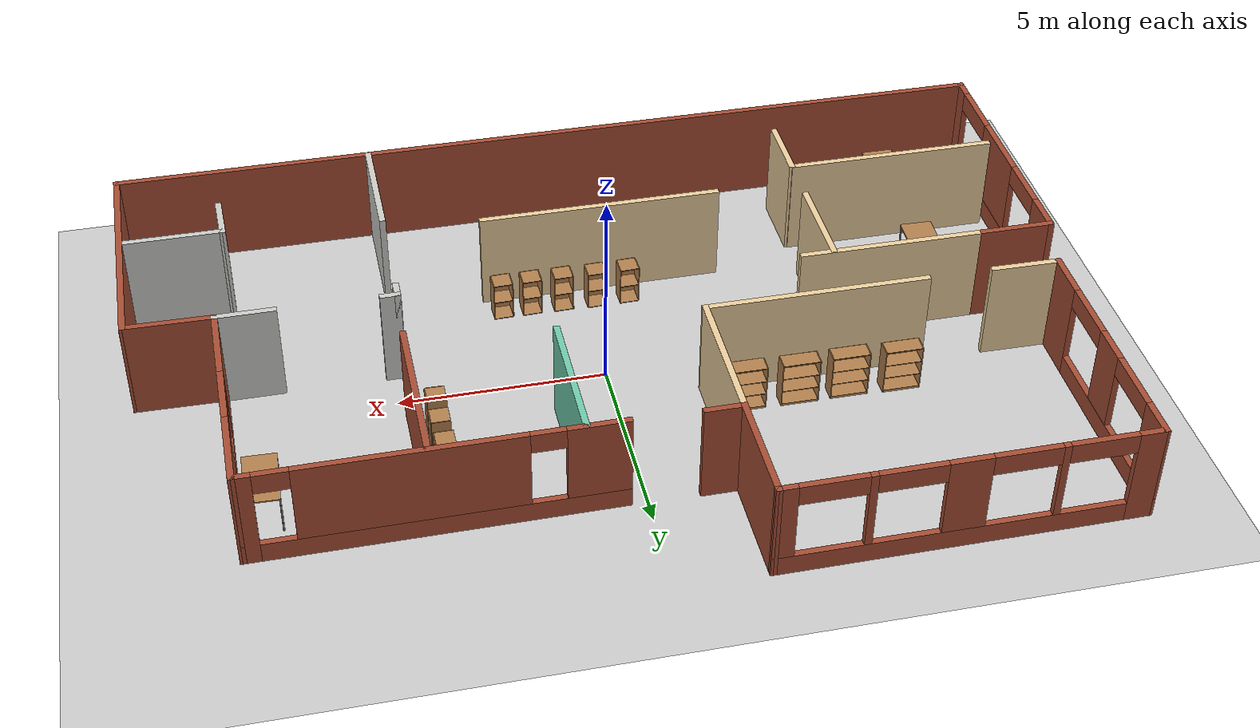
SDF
<sdf version="1.6">
 <world name="default">
  <plugin name="hello" filename="libhello.so"/>
  <light name="sun" type="directional">
   <pose>0 0 10 0 -0 0</pose>
   <diffuse>0.8 0.8 0.8 1</diffuse>
   <specular>0.2 0.2 0.2 1</specular>
   <attenuation>
    <range>1000</range>
    <constant>0.9</constant>
    <linear>0.01</linear>
    <quadratic>0.001</quadratic>
   </attenuation>
   <direction>-0.5 0.1 -0.9</direction>
  </light>
  <model name="ground_plane">
   <static>1</static>
   <link name="link">
    <collision name="collision">
     <geometry><plane><normal>0 0 1</normal><size>100 100</size></plane></geometry>
     <surface><friction><ode><mu>100</mu><mu2>50</mu2></ode></friction></surface>
    </collision>
    <visual name="visual">
     <cast_shadows>0</cast_shadows>
     <geometry><plane><normal>0 0 1</normal><size>100 100</size></plane></geometry>
     <material>
      <script><uri>file://media/materials/scripts/gazebo.material</uri><name>Gazebo/Grey</name></script>
     </material>
    </visual>
   </link>
  </model>
  <gravity>0 0 -9.8</gravity>
  <magnetic_field>6e-06 2.3e-05 -4.2e-05</magnetic_field>
  <atmosphere type="adiabatic"/>
  <physics name="default_physics" default="0" type="ode">
   <max_step_size>0.001</max_step_size>
   <real_time_factor>1</real_time_factor>
   <real_time_update_rate>1000</real_time_update_rate>
  </physics>
  <scene><ambient>0.4 0.4 0.4 1</ambient><background>0.7 0.7 0.7 1</background><shadows>1</shadows></scene>
  <spherical_coordinates>
   <surface_model>EARTH_WGS84</surface_model>
   <latitude_deg>0</latitude_deg>
   <longitude_deg>0</longitude_deg>
   <elevation>0</elevation>
   <heading_deg>0</heading_deg>
  </spherical_coordinates>
  <model name="Building">
   <pose>-0.04157 0.13708 0 0 -0 0</pose>
   <link name="Wall_0">
    <pose>-6.38643 6.94192 0 0 -0 0.004651</pose>
    <visual name="Wall_0_Visual_0">
     <pose>-4.03681 0 1.25 0 -0 0</pose>
     <geometry><box><size>0.676483 0.15 2.5</size></box></geometry>
     <material>
      <script><uri>file://media/materials/scripts/gazebo.material</uri><name>Gazebo/Bricks</name></script>
      <ambient>1 1 1 1</ambient>
     </material>
     <meta><layer>0</layer></meta>
    </visual>
    <collision name="Wall_0_Collision_0">
     <geometry><box><size>0.676483 0.15 2.5</size></box></geometry>
     <pose>-4.03681 0 1.25 0 -0 0</pose>
    </collision>
    <visual name="Wall_0_Visual_1">
     <pose>0.338242 0 0.25 0 -0 0</pose>
     <geometry><box><size>8.07361 0.15 0.5</size></box></geometry>
     <material>
      <script><uri>file://media/materials/scripts/gazebo.material</uri><name>Gazebo/Bricks</name></script>
      <ambient>1 1 1 1</ambient>
     </material>
     <meta><layer>0</layer></meta>
    </visual>
    <collision name="Wall_0_Collision_1">
     <geometry><box><size>8.07361 0.15 0.5</size></box></geometry>
     <pose>0.338242 0 0.25 0 -0 0</pose>
    </collision>
    <visual name="Wall_0_Visual_2">
     <pose>-2.05817 0 1.5 0 -0 0</pose>
     <geometry><box><size>0.164796 0.15 2</size></box></geometry>
     <material>
      <script><uri>file://media/materials/scripts/gazebo.material</uri><name>Gazebo/Bricks</name></script>
      <ambient>1 1 1 1</ambient>
     </material>
     <meta><layer>0</layer></meta>
    </visual>
    <collision name="Wall_0_Collision_2">
     <geometry><box><size>0.164796 0.15 2</size></box></geometry>
     <pose>-2.05817 0 1.5 0 -0 0</pose>
    </collision>
    <visual name="Wall_0_Visual_3">
     <pose>0.078861 0 1.5 0 -0 0</pose>
     <geometry><box><size>0.993258 0.15 2</size></box></geometry>
     <material>
      <script><uri>file://media/materials/scripts/gazebo.material</uri><name>Gazebo/Bricks</name></script>
      <ambient>1 1 1 1</ambient>
     </material>
     <meta><layer>0</layer></meta>
    </visual>
    <collision name="Wall_0_Collision_3">
     <geometry><box><size>0.993258 0.15 2</size></box></geometry>
     <pose>0.078861 0 1.5 0 -0 0</pose>
    </collision>
    <visual name="Wall_0_Visual_4">
     <pose>2.22237 0 1.5 0 -0 0</pose>
     <geometry><box><size>0.177762 0.15 2</size></box></geometry>
     <material>
      <script><uri>file://media/materials/scripts/gazebo.material</uri><name>Gazebo/Bricks</name></script>
      <ambient>1 1 1 1</ambient>
     </material>
     <meta><layer>0</layer></meta>
    </visual>
    <collision name="Wall_0_Collision_4">
     <geometry><box><size>0.177762 0.15 2</size></box></geometry>
     <pose>2.22237 0 1.5 0 -0 0</pose>
    </collision>
    <visual name="Wall_0_Visual_5">
     <pose>4.12215 0 1.5 0 -0 0</pose>
     <geometry><box><size>0.505795 0.15 2</size></box></geometry>
     <material>
      <script><uri>file://media/materials/scripts/gazebo.material</uri><name>Gazebo/Bricks</name></script>
      <ambient>1 1 1 1</ambient>
     </material>
     <meta><layer>0</layer></meta>
    </visual>
    <collision name="Wall_0_Collision_5">
     <geometry><box><size>0.505795 0.15 2</size></box></geometry>
     <pose>4.12215 0 1.5 0 -0 0</pose>
    </collision>
    <visual name="Wall_0_Visual_6">
     <pose>-2.91956 0 2.25 0 -0 0</pose>
     <geometry><box><size>1.558 0.15 0.5</size></box></geometry>
     <material>
      <script><uri>file://media/materials/scripts/gazebo.material</uri><name>Gazebo/Bricks</name></script>
      <ambient>1 1 1 1</ambient>
     </material>
     <meta><layer>0</layer></meta>
    </visual>
    <collision name="Wall_0_Collision_6">
     <geometry><box><size>1.558 0.15 0.5</size></box></geometry>
     <pose>-2.91956 0 2.25 0 -0 0</pose>
    </collision>
    <visual name="Wall_0_Visual_7">
     <pose>-1.19677 0 2.25 0 -0 0</pose>
     <geometry><box><size>1.558 0.15 0.5</size></box></geometry>
     <material>
      <script><uri>file://media/materials/scripts/gazebo.material</uri><name>Gazebo/Bricks</name></script>
      <ambient>1 1 1 1</ambient>
     </material>
     <meta><layer>0</layer></meta>
    </visual>
    <collision name="Wall_0_Collision_7">
     <geometry><box><size>1.558 0.15 0.5</size></box></geometry>
     <pose>-1.19677 0 2.25 0 -0 0</pose>
    </collision>
    <visual name="Wall_0_Visual_8">
     <pose>1.35449 0 2.25 0 -0 0</pose>
     <geometry><box><size>1.558 0.15 0.5</size></box></geometry>
     <material>
      <script><uri>file://media/materials/scripts/gazebo.material</uri><name>Gazebo/Bricks</name></script>
      <ambient>1 1 1 1</ambient>
     </material>
     <meta><layer>0</layer></meta>
    </visual>
    <collision name="Wall_0_Collision_8">
     <geometry><box><size>1.558 0.15 0.5</size></box></geometry>
     <pose>1.35449 0 2.25 0 -0 0</pose>
    </collision>
    <visual name="Wall_0_Visual_9">
     <pose>3.09025 0 2.25 0 -0 0</pose>
     <geometry><box><size>1.558 0.15 0.5</size></box></geometry>
     <material>
      <script><uri>file://media/materials/scripts/gazebo.material</uri><name>Gazebo/Bricks</name></script>
      <ambient>1 1 1 1</ambient>
     </material>
     <meta><layer>0</layer></meta>
    </visual>
    <collision name="Wall_0_Collision_9">
     <geometry><box><size>1.558 0.15 0.5</size></box></geometry>
     <pose>3.09025 0 2.25 0 -0 0</pose>
    </collision>
   </link>
   <link name="Wall_10">
    <pose>-11.0594 -3.78708 0 0 0 -1.5708</pose>
    <visual name="Wall_10_Visual_0">
     <pose>-2.71387 0 1.25 0 -0 0</pose>
     <geometry><box><size>1.07227 0.15 2.5</size></box></geometry>
     <material>
      <script><uri>file://media/materials/scripts/gazebo.material</uri><name>Gazebo/Bricks</name></script>
      <ambient>1 1 1 1</ambient>
     </material>
     <meta><layer>0</layer></meta>
    </visual>
    <collision name="Wall_10_Collision_0">
     <geometry><box><size>1.07227 0.15 2.5</size></box></geometry>
     <pose>-2.71387 0 1.25 0 -0 0</pose>
    </collision>
    <visual name="Wall_10_Visual_1">
     <pose>0.536132 0 0.25 0 -0 0</pose>
     <geometry><box><size>5.42774 0.15 0.5</size></box></geometry>
     <material>
      <script><uri>file://media/materials/scripts/gazebo.material</uri><name>Gazebo/Bricks</name></script>
      <ambient>1 1 1 1</ambient>
     </material>
     <meta><layer>0</layer></meta>
    </visual>
    <collision name="Wall_10_Collision_1">
     <geometry><box><size>5.42774 0.15 0.5</size></box></geometry>
     <pose>0.536132 0 0.25 0 -0 0</pose>
    </collision>
    <visual name="Wall_10_Visual_2">
     <pose>0.214444 0 1.5 0 -0 0</pose>
     <geometry><box><size>1.92236 0.15 2</size></box></geometry>
     <material>
      <script><uri>file://media/materials/scripts/gazebo.material</uri><name>Gazebo/Bricks</name></script>
      <ambient>1 1 1 1</ambient>
     </material>
     <meta><layer>0</layer></meta>
    </visual>
    <collision name="Wall_10_Collision_2">
     <geometry><box><size>1.92236 0.15 2</size></box></geometry>
     <pose>0.214444 0 1.5 0 -0 0</pose>
    </collision>
    <visual name="Wall_10_Visual_3">
     <pose>2.97431 0 1.5 0 -0 0</pose>
     <geometry><box><size>0.551376 0.15 2</size></box></geometry>
     <material>
      <script><uri>file://media/materials/scripts/gazebo.material</uri><name>Gazebo/Bricks</name></script>
      <ambient>1 1 1 1</ambient>
     </material>
     <meta><layer>0</layer></meta>
    </visual>
    <collision name="Wall_10_Collision_3">
     <geometry><box><size>0.551376 0.15 2</size></box></geometry>
     <pose>2.97431 0 1.5 0 -0 0</pose>
    </collision>
    <visual name="Wall_10_Visual_4">
     <pose>-1.46223 0 2.25 0 -0 0</pose>
     <geometry><box><size>1.431 0.15 0.5</size></box></geometry>
     <material>
      <script><uri>file://media/materials/scripts/gazebo.material</uri><name>Gazebo/Bricks</name></script>
      <ambient>1 1 1 1</ambient>
     </material>
     <meta><layer>0</layer></meta>
    </visual>
    <collision name="Wall_10_Collision_4">
     <geometry><box><size>1.431 0.15 0.5</size></box></geometry>
     <pose>-1.46223 0 2.25 0 -0 0</pose>
    </collision>
    <visual name="Wall_10_Visual_5">
     <pose>1.93712 0 2.25 0 -0 0</pose>
     <geometry><box><size>1.523 0.15 0.5</size></box></geometry>
     <material>
      <script><uri>file://media/materials/scripts/gazebo.material</uri><name>Gazebo/Bricks</name></script>
      <ambient>1 1 1 1</ambient>
     </material>
     <meta><layer>0</layer></meta>
    </visual>
    <collision name="Wall_10_Collision_5">
     <geometry><box><size>1.523 0.15 0.5</size></box></geometry>
     <pose>1.93712 0 2.25 0 -0 0</pose>
    </collision>
   </link>
   <link name="Wall_11">
    <collision name="Wall_11_Collision">
     <geometry><box><size>22.25 0.15 2.5</size></box></geometry>
     <pose>0 0 1.25 0 -0 0</pose>
    </collision>
    <visual name="Wall_11_Visual">
     <pose>0 0 1.25 0 -0 0</pose>
     <geometry><box><size>22.25 0.15 2.5</size></box></geometry>
     <material>
      <script><uri>file://media/materials/scripts/gazebo.material</uri><name>Gazebo/Bricks</name></script>
      <ambient>1 1 1 1</ambient>
     </material>
     <meta><layer>0</layer></meta>
    </visual>
    <pose>-0.009426 -6.96208 0 0 -0 0</pose>
   </link>
   <link name="Wall_12">
    <collision name="Wall_12_Collision">
     <geometry><box><size>5.93893 0.15 2.5</size></box></geometry>
     <pose>0 0 1.25 0 -0 0</pose>
    </collision>
    <visual name="Wall_12_Visual">
     <pose>0 0 1.25 0 -0 0</pose>
     <geometry><box><size>5.93893 0.15 2.5</size></box></geometry>
     <material>
      <script><uri>file://media/materials/scripts/gazebo.material</uri><name>Gazebo/Bricks</name></script>
      <ambient>1 1 1 1</ambient>
     </material>
     <meta><layer>0</layer></meta>
    </visual>
    <pose>11.0496 -4.06758 0 0 -0 1.56769</pose>
   </link>
   <link name="Wall_13">
    <collision name="Wall_13_Collision">
     <geometry><box><size>2.21989 0.15 2.5</size></box></geometry>
     <pose>0 0 1.25 0 -0 0</pose>
    </collision>
    <visual name="Wall_13_Visual">
     <pose>0 0 1.25 0 -0 0</pose>
     <geometry><box><size>2.21989 0.15 2.5</size></box></geometry>
     <material>
      <script><uri>file://media/materials/scripts/gazebo.material</uri><name>Gazebo/Bricks</name></script>
      <ambient>1 1 1 1</ambient>
     </material>
     <meta><layer>0</layer></meta>
    </visual>
    <pose>10.0236 -1.15758 0 0 -0 3.12662</pose>
   </link>
   <link name="Wall_14">
    <pose>8.98107 1.57092 0 0 -0 1.57356</pose>
    <visual name="Wall_14_Visual_0">
     <pose>-1.77321 0 1.25 0 -0 0</pose>
     <geometry><box><size>2.02965 0.15 2.5</size></box></geometry>
     <material>
      <script><uri>file://media/materials/scripts/gazebo.material</uri><name>Gazebo/Bricks</name></script>
      <ambient>1 1 1 1</ambient>
     </material>
     <meta><layer>0</layer></meta>
    </visual>
    <collision name="Wall_14_Collision_0">
     <geometry><box><size>2.02965 0.15 2.5</size></box></geometry>
     <pose>-1.77321 0 1.25 0 -0 0</pose>
    </collision>
    <visual name="Wall_14_Visual_1">
     <pose>1.01483 0 0.25 0 -0 0</pose>
     <geometry><box><size>3.54641 0.15 0.5</size></box></geometry>
     <material>
      <script><uri>file://media/materials/scripts/gazebo.material</uri><name>Gazebo/Bricks</name></script>
      <ambient>1 1 1 1</ambient>
     </material>
     <meta><layer>0</layer></meta>
    </visual>
    <collision name="Wall_14_Collision_1">
     <geometry><box><size>3.54641 0.15 0.5</size></box></geometry>
     <pose>1.01483 0 0.25 0 -0 0</pose>
    </collision>
    <visual name="Wall_14_Visual_2">
     <pose>1.78283 0 1.5 0 -0 0</pose>
     <geometry><box><size>2.01041 0.15 2</size></box></geometry>
     <material>
      <script><uri>file://media/materials/scripts/gazebo.material</uri><name>Gazebo/Bricks</name></script>
      <ambient>1 1 1 1</ambient>
     </material>
     <meta><layer>0</layer></meta>
    </visual>
    <collision name="Wall_14_Collision_2">
     <geometry><box><size>2.01041 0.15 2</size></box></geometry>
     <pose>1.78283 0 1.5 0 -0 0</pose>
    </collision>
    <visual name="Wall_14_Visual_3">
     <pose>0.009621 0 2.25 0 -0 0</pose>
     <geometry><box><size>1.536 0.15 0.5</size></box></geometry>
     <material>
      <script><uri>file://media/materials/scripts/gazebo.material</uri><name>Gazebo/Bricks</name></script>
      <ambient>1 1 1 1</ambient>
     </material>
     <meta><layer>0</layer></meta>
    </visual>
    <collision name="Wall_14_Collision_3">
     <geometry><box><size>1.536 0.15 0.5</size></box></geometry>
     <pose>0.009621 0 2.25 0 -0 0</pose>
    </collision>
   </link>
   <link name="Wall_15">
    <pose>4.71957 4.26092 0 0 0 -3.13619</pose>
    <visual name="Wall_15_Visual_0">
     <pose>-4.09017 0 1.25 0 -0 0</pose>
     <geometry><box><size>0.478412 0.15 2.5</size></box></geometry>
     <material>
      <script><uri>file://media/materials/scripts/gazebo.material</uri><name>Gazebo/Bricks</name></script>
      <ambient>1 1 1 1</ambient>
     </material>
     <meta><layer>0</layer></meta>
    </visual>
    <collision name="Wall_15_Collision_0">
     <geometry><box><size>0.478412 0.15 2.5</size></box></geometry>
     <pose>-4.09017 0 1.25 0 -0 0</pose>
    </collision>
    <visual name="Wall_15_Visual_1">
     <pose>0.239206 0 0.25 0 -0 0</pose>
     <geometry><box><size>8.18035 0.15 0.5</size></box></geometry>
     <material>
      <script><uri>file://media/materials/scripts/gazebo.material</uri><name>Gazebo/Bricks</name></script>
      <ambient>1 1 1 1</ambient>
     </material>
     <meta><layer>0</layer></meta>
    </visual>
    <collision name="Wall_15_Collision_1">
     <geometry><box><size>8.18035 0.15 0.5</size></box></geometry>
     <pose>0.239206 0 0.25 0 -0 0</pose>
    </collision>
    <visual name="Wall_15_Visual_2">
     <pose>-0.485949 0 1.5 0 -0 0</pose>
     <geometry><box><size>5.13004 0.15 2</size></box></geometry>
     <material>
      <script><uri>file://media/materials/scripts/gazebo.material</uri><name>Gazebo/Bricks</name></script>
      <ambient>1 1 1 1</ambient>
     </material>
     <meta><layer>0</layer></meta>
    </visual>
    <collision name="Wall_15_Collision_2">
     <geometry><box><size>5.13004 0.15 2</size></box></geometry>
     <pose>-0.485949 0 1.5 0 -0 0</pose>
    </collision>
    <visual name="Wall_15_Visual_3">
     <pose>3.60423 0 1.5 0 -0 0</pose>
     <geometry><box><size>1.45031 0.15 2</size></box></geometry>
     <material>
      <script><uri>file://media/materials/scripts/gazebo.material</uri><name>Gazebo/Bricks</name></script>
      <ambient>1 1 1 1</ambient>
     </material>
     <meta><layer>0</layer></meta>
    </visual>
    <collision name="Wall_15_Collision_3">
     <geometry><box><size>1.45031 0.15 2</size></box></geometry>
     <pose>3.60423 0 1.5 0 -0 0</pose>
    </collision>
    <visual name="Wall_15_Visual_4">
     <pose>-3.45097 0 2.25 0 -0 0</pose>
     <geometry><box><size>0.8 0.15 0.5</size></box></geometry>
     <material>
      <script><uri>file://media/materials/scripts/gazebo.material</uri><name>Gazebo/Bricks</name></script>
      <ambient>1 1 1 1</ambient>
     </material>
     <meta><layer>0</layer></meta>
    </visual>
    <collision name="Wall_15_Collision_4">
     <geometry><box><size>0.8 0.15 0.5</size></box></geometry>
     <pose>-3.45097 0 2.25 0 -0 0</pose>
    </collision>
    <visual name="Wall_15_Visual_5">
     <pose>2.47907 0 2.25 0 -0 0</pose>
     <geometry><box><size>0.8 0.15 0.5</size></box></geometry>
     <material>
      <script><uri>file://media/materials/scripts/gazebo.material</uri><name>Gazebo/Bricks</name></script>
      <ambient>1 1 1 1</ambient>
     </material>
     <meta><layer>0</layer></meta>
    </visual>
    <collision name="Wall_15_Collision_5">
     <geometry><box><size>0.8 0.15 0.5</size></box></geometry>
     <pose>2.47907 0 2.25 0 -0 0</pose>
    </collision>
   </link>
   <link name="Wall_17">
    <collision name="Wall_17_Collision">
     <geometry><box><size>1 0.15 2.5</size></box></geometry>
     <pose>0 0 1.25 0 -0 0</pose>
    </collision>
    <visual name="Wall_17_Visual">
     <pose>0 0 1.25 0 -0 0</pose>
     <geometry><box><size>1 0.15 2.5</size></box></geometry>
     <material>
      <script><uri>file://media/materials/scripts/gazebo.material</uri><name>Gazebo/Bricks</name></script>
      <ambient>1 1 1 1</ambient>
     </material>
     <meta><layer>0</layer></meta>
    </visual>
    <pose>-1.65643 4.28292 0 0 -0 0</pose>
   </link>
   <link name="Wall_19">
    <collision name="Wall_19_Collision">
     <geometry><box><size>2.5 0.15 2.5</size></box></geometry>
     <pose>0 0 1.25 0 -0 0</pose>
    </collision>
    <visual name="Wall_19_Visual">
     <pose>0 0 1.25 0 -0 0</pose>
     <geometry><box><size>2.5 0.15 2.5</size></box></geometry>
     <material>
      <script><uri>file://media/materials/scripts/gazebo.material</uri><name>Gazebo/Grey</name></script>
      <ambient>0.921569 0.807843 0.615686 1</ambient>
     </material>
     <meta><layer>0</layer></meta>
    </visual>
    <pose>-5.59943 -1.81708 0 0 0 -1.5708</pose>
   </link>
   <link name="Wall_2">
    <collision name="Wall_2_Collision">
     <geometry><box><size>5.5 0.15 2.5</size></box></geometry>
     <pose>0 0 1.25 0 -0 0</pose>
    </collision>
    <visual name="Wall_2_Visual">
     <pose>0 0 1.25 0 -0 0</pose>
     <geometry><box><size>5.5 0.15 2.5</size></box></geometry>
     <material>
      <script><uri>file://media/materials/scripts/gazebo.material</uri><name>Gazebo/Grey</name></script>
      <ambient>0.921569 0.807843 0.615686 1</ambient>
     </material>
     <meta><layer>0</layer></meta>
    </visual>
    <pose>-4.76143 0.821919 0 0 -0 3.14159</pose>
   </link>
   <link name="Wall_21">
    <collision name="Wall_21_Collision">
     <geometry><box><size>1.75 0.15 2.5</size></box></geometry>
     <pose>0 0 1.25 0 -0 0</pose>
    </collision>
    <visual name="Wall_21_Visual">
     <pose>0 0 1.25 0 -0 0</pose>
     <geometry><box><size>1.75 0.15 2.5</size></box></geometry>
     <material>
      <script><uri>file://media/materials/scripts/gazebo.material</uri><name>Gazebo/Grey</name></script>
      <ambient>0.921569 0.807843 0.615686 1</ambient>
     </material>
     <meta><layer>0</layer></meta>
    </visual>
    <pose>-5.59943 -5.05208 0 0 0 -1.5708</pose>
   </link>
   <link name="Wall_23">
    <collision name="Wall_23_Collision">
     <geometry><box><size>5.25 0.15 2.5</size></box></geometry>
     <pose>0 0 1.25 0 -0 0</pose>
    </collision>
    <visual name="Wall_23_Visual">
     <pose>0 0 1.25 0 -0 0</pose>
     <geometry><box><size>5.25 0.15 2.5</size></box></geometry>
     <material>
      <script><uri>file://media/materials/scripts/gazebo.material</uri><name>Gazebo/Grey</name></script>
      <ambient>0.921569 0.807843 0.615686 1</ambient>
     </material>
     <meta><layer>0</layer></meta>
    </visual>
    <pose>-8.21943 -4.22108 0 0 -0 0</pose>
   </link>
   <link name="Wall_26">
    <collision name="Wall_26_Collision">
     <geometry><box><size>6 0.15 2.5</size></box></geometry>
     <pose>0 0 1.25 0 -0 0</pose>
    </collision>
    <visual name="Wall_26_Visual">
     <pose>0 0 1.25 0 -0 0</pose>
     <geometry><box><size>6 0.15 2.5</size></box></geometry>
     <material>
      <script><uri>file://media/materials/scripts/gazebo.material</uri><name>Gazebo/Grey</name></script>
      <ambient>0.921569 0.807843 0.615686 1</ambient>
     </material>
     <meta><layer>0</layer></meta>
    </visual>
    <pose>-0.533426 -3.57908 0 0 -0 0</pose>
   </link>
   <link name="Wall_30">
    <collision name="Wall_30_Collision">
     <geometry><box><size>3.5 0.15 2.5</size></box></geometry>
     <pose>0 0 1.25 0 -0 0</pose>
    </collision>
    <visual name="Wall_30_Visual">
     <pose>0 0 1.25 0 -0 0</pose>
     <geometry><box><size>3.5 0.15 2.5</size></box></geometry>
     <material>
      <script><uri>file://media/materials/scripts/gazebo.material</uri><name>Gazebo/Grey</name></script>
      <ambient>0.435294 0.796078 0.67451 1</ambient>
     </material>
     <meta><layer>0</layer></meta>
    </visual>
    <pose>1.40557 2.54692 0 0 0 -1.5708</pose>
   </link>
   <link name="Wall_32">
    <collision name="Wall_32_Collision">
     <geometry><box><size>0.5 0.15 2.5</size></box></geometry>
     <pose>0 0 1.25 0 -0 0</pose>
    </collision>
    <visual name="Wall_32_Visual">
     <pose>0 0 1.25 0 -0 0</pose>
     <geometry><box><size>0.5 0.15 2.5</size></box></geometry>
     <material>
      <script><uri>file://media/materials/scripts/gazebo.material</uri><name>Gazebo/CeilingTiled</name></script>
      <ambient>1 1 1 1</ambient>
     </material>
     <meta><layer>0</layer></meta>
    </visual>
    <pose>4.77857 -1.28608 0 0 -0 1.5708</pose>
   </link>
   <link name="Wall_33">
    <collision name="Wall_33_Collision">
     <geometry><box><size>0.5 0.15 2.5</size></box></geometry>
     <pose>0 0 1.25 0 -0 0</pose>
    </collision>
    <visual name="Wall_33_Visual">
     <pose>0 0 1.25 0 -0 0</pose>
     <geometry><box><size>0.5 0.15 2.5</size></box></geometry>
     <material>
      <script><uri>file://media/materials/scripts/gazebo.material</uri><name>Gazebo/CeilingTiled</name></script>
      <ambient>1 1 1 1</ambient>
     </material>
     <meta><layer>0</layer></meta>
    </visual>
    <pose>4.95357 -1.11108 0 0 -0 0</pose>
   </link>
   <link name="Wall_35">
    <collision name="Wall_35_Collision">
     <geometry><box><size>1.5 0.15 2.5</size></box></geometry>
     <pose>0 0 1.25 0 -0 0</pose>
    </collision>
    <visual name="Wall_35_Visual">
     <pose>0 0 1.25 0 -0 0</pose>
     <geometry><box><size>1.5 0.15 2.5</size></box></geometry>
     <material>
      <script><uri>file://media/materials/scripts/gazebo.material</uri><name>Gazebo/CeilingTiled</name></script>
      <ambient>1 1 1 1</ambient>
     </material>
     <meta><layer>0</layer></meta>
    </visual>
    <pose>8.31357 -1.14208 0 0 -0 0</pose>
   </link>
   <link name="Wall_37">
    <collision name="Wall_37_Collision">
     <geometry><box><size>2.46292 0.15 2.5</size></box></geometry>
     <pose>0 0 1.25 0 -0 0</pose>
    </collision>
    <visual name="Wall_37_Visual">
     <pose>0 0 1.25 0 -0 0</pose>
     <geometry><box><size>2.46292 0.15 2.5</size></box></geometry>
     <material>
      <script><uri>file://media/materials/scripts/gazebo.material</uri><name>Gazebo/CeilingTiled</name></script>
      <ambient>1 1 1 1</ambient>
     </material>
     <meta><layer>0</layer></meta>
    </visual>
    <pose>9.74857 -4.43108 0 0 -0 3.14159</pose>
   </link>
   <link name="Wall_38">
    <collision name="Wall_38_Collision">
     <geometry><box><size>1.25 0.15 2.5</size></box></geometry>
     <pose>0 0 1.25 0 -0 0</pose>
    </collision>
    <visual name="Wall_38_Visual">
     <pose>0 0 1.25 0 -0 0</pose>
     <geometry><box><size>1.25 0.15 2.5</size></box></geometry>
     <material>
      <script><uri>file://media/materials/scripts/gazebo.material</uri><name>Gazebo/CeilingTiled</name></script>
      <ambient>1 1 1 1</ambient>
     </material>
     <meta><layer>0</layer></meta>
    </visual>
    <pose>8.60757 -4.98108 0 0 0 -1.54353</pose>
   </link>
   <link name="Wall_4">
    <collision name="Wall_4_Collision">
     <geometry><box><size>1.75 0.15 2.5</size></box></geometry>
     <pose>0 0 1.25 0 -0 0</pose>
    </collision>
    <visual name="Wall_4_Visual">
     <pose>0 0 1.25 0 -0 0</pose>
     <geometry><box><size>1.75 0.15 2.5</size></box></geometry>
     <material>
      <script><uri>file://media/materials/scripts/gazebo.material</uri><name>Gazebo/Grey</name></script>
      <ambient>0.921569 0.807843 0.615686 1</ambient>
     </material>
     <meta><layer>0</layer></meta>
    </visual>
    <pose>-9.88643 0.831919 0 0 -0 3.12909</pose>
   </link>
   <link name="Wall_40">
    <collision name="Wall_40_Collision">
     <geometry><box><size>3 0.15 2.5</size></box></geometry>
     <pose>0 0 1.25 0 -0 0</pose>
    </collision>
    <visual name="Wall_40_Visual">
     <pose>0 0 1.25 0 -0 0</pose>
     <geometry><box><size>3 0.15 2.5</size></box></geometry>
     <material>
      <script><uri>file://media/materials/scripts/gazebo.material</uri><name>Gazebo/CeilingTiled</name></script>
      <ambient>1 1 1 1</ambient>
     </material>
     <meta><layer>0</layer></meta>
    </visual>
    <pose>4.76557 -5.52308 0 0 -0 1.5708</pose>
   </link>
   <link name="Wall_42">
    <collision name="Wall_42_Collision">
     <geometry><box><size>4 0.15 2.5</size></box></geometry>
     <pose>0 0 1.25 0 -0 0</pose>
    </collision>
    <visual name="Wall_42_Visual">
     <pose>0 0 1.25 0 -0 0</pose>
     <geometry><box><size>4 0.15 2.5</size></box></geometry>
     <material>
      <script><uri>file://media/materials/scripts/gazebo.material</uri><name>Gazebo/Bricks</name></script>
      <ambient>1 1 1 1</ambient>
     </material>
     <meta><layer>0</layer></meta>
    </visual>
    <pose>4.84357 2.25192 0 0 0 -1.5708</pose>
   </link>
   <link name="Wall_5">
    <pose>-10.6864 3.88192 0 0 -0 1.5708</pose>
    <visual name="Wall_5_Visual_0">
     <pose>-2.49798 0 1.25 0 -0 0</pose>
     <geometry><box><size>1.23397 0.15 2.5</size></box></geometry>
     <material>
      <script><uri>file://media/materials/scripts/gazebo.material</uri><name>Gazebo/Bricks</name></script>
      <ambient>1 1 1 1</ambient>
     </material>
     <meta><layer>0</layer></meta>
    </visual>
    <collision name="Wall_5_Collision_0">
     <geometry><box><size>1.23397 0.15 2.5</size></box></geometry>
     <pose>-2.49798 0 1.25 0 -0 0</pose>
    </collision>
    <visual name="Wall_5_Visual_1">
     <pose>0.616984 0 0.25 0 -0 0</pose>
     <geometry><box><size>4.99595 0.15 0.5</size></box></geometry>
     <material>
      <script><uri>file://media/materials/scripts/gazebo.material</uri><name>Gazebo/Bricks</name></script>
      <ambient>1 1 1 1</ambient>
     </material>
     <meta><layer>0</layer></meta>
    </visual>
    <collision name="Wall_5_Collision_1">
     <geometry><box><size>4.99595 0.15 0.5</size></box></geometry>
     <pose>0.616984 0 0.25 0 -0 0</pose>
    </collision>
    <visual name="Wall_5_Visual_2">
     <pose>0.133921 0 1.5 0 -0 0</pose>
     <geometry><box><size>0.969686 0.15 2</size></box></geometry>
     <material>
      <script><uri>file://media/materials/scripts/gazebo.material</uri><name>Gazebo/Bricks</name></script>
      <ambient>1 1 1 1</ambient>
     </material>
     <meta><layer>0</layer></meta>
    </visual>
    <collision name="Wall_5_Collision_2">
     <geometry><box><size>0.969686 0.15 2</size></box></geometry>
     <pose>0.133921 0 1.5 0 -0 0</pose>
    </collision>
    <visual name="Wall_5_Visual_3">
     <pose>2.63186 0 1.5 0 -0 0</pose>
     <geometry><box><size>0.966196 0.15 2</size></box></geometry>
     <material>
      <script><uri>file://media/materials/scripts/gazebo.material</uri><name>Gazebo/Bricks</name></script>
      <ambient>1 1 1 1</ambient>
     </material>
     <meta><layer>0</layer></meta>
    </visual>
    <collision name="Wall_5_Collision_3">
     <geometry><box><size>0.966196 0.15 2</size></box></geometry>
     <pose>2.63186 0 1.5 0 -0 0</pose>
    </collision>
    <visual name="Wall_5_Visual_4">
     <pose>-1.11596 0 2.25 0 -0 0</pose>
     <geometry><box><size>1.53007 0.15 0.5</size></box></geometry>
     <material>
      <script><uri>file://media/materials/scripts/gazebo.material</uri><name>Gazebo/Bricks</name></script>
      <ambient>1 1 1 1</ambient>
     </material>
     <meta><layer>0</layer></meta>
    </visual>
    <collision name="Wall_5_Collision_4">
     <geometry><box><size>1.53007 0.15 0.5</size></box></geometry>
     <pose>-1.11596 0 2.25 0 -0 0</pose>
    </collision>
    <visual name="Wall_5_Visual_5">
     <pose>1.38376 0 2.25 0 -0 0</pose>
     <geometry><box><size>1.53 0.15 0.5</size></box></geometry>
     <material>
      <script><uri>file://media/materials/scripts/gazebo.material</uri><name>Gazebo/Bricks</name></script>
      <ambient>1 1 1 1</ambient>
     </material>
     <meta><layer>0</layer></meta>
    </visual>
    <collision name="Wall_5_Collision_5">
     <geometry><box><size>1.53 0.15 0.5</size></box></geometry>
     <pose>1.38376 0 2.25 0 -0 0</pose>
    </collision>
   </link>
   <link name="Wall_71">
    <collision name="Wall_71_Collision">
     <geometry><box><size>2.82905 0.15 2.5</size></box></geometry>
     <pose>0 0 1.25 0 -0 0</pose>
    </collision>
    <visual name="Wall_71_Visual">
     <pose>0 0 1.25 0 -0 0</pose>
     <geometry><box><size>2.82905 0.15 2.5</size></box></geometry>
     <material>
      <script><uri>file://media/materials/scripts/gazebo.material</uri><name>Gazebo/Bricks</name></script>
      <ambient>1 1 1 1</ambient>
     </material>
     <meta><layer>0</layer></meta>
    </visual>
    <pose>-2.08393 5.62242 0 0 0 -1.56893</pose>
   </link>
   <link name="Wall_73">
    <collision name="Wall_73_Collision">
     <geometry><box><size>3.61119 0.15 2.5</size></box></geometry>
     <pose>0 0 1.25 0 -0 0</pose>
    </collision>
    <visual name="Wall_73_Visual">
     <pose>0 0 1.25 0 -0 0</pose>
     <geometry><box><size>3.61119 0.15 2.5</size></box></geometry>
     <material>
      <script><uri>file://media/materials/scripts/gazebo.material</uri><name>Gazebo/Grey</name></script>
      <ambient>0.921569 0.807843 0.615686 1</ambient>
     </material>
     <meta><layer>0</layer></meta>
    </visual>
    <pose>-2.08393 2.55242 0 0 0 -1.57224</pose>
   </link>
   <link name="Wall_75">
    <collision name="Wall_75_Collision">
     <geometry><box><size>4.5 0.15 2.5</size></box></geometry>
     <pose>0 0 1.25 0 -0 0</pose>
    </collision>
    <visual name="Wall_75_Visual">
     <pose>0 0 1.25 0 -0 0</pose>
     <geometry><box><size>4.5 0.15 2.5</size></box></geometry>
     <material>
      <script><uri>file://media/materials/scripts/gazebo.material</uri><name>Gazebo/Grey</name></script>
      <ambient>0.921569 0.807843 0.615686 1</ambient>
     </material>
     <meta><layer>0</layer></meta>
    </visual>
    <pose>-7.01943 -0.612081 0 0 -0 0</pose>
   </link>
   <link name="Wall_9">
    <collision name="Wall_9_Collision">
     <geometry><box><size>2.01518 0.15 2.5</size></box></geometry>
     <pose>0 0 1.25 0 -0 0</pose>
    </collision>
    <visual name="Wall_9_Visual">
     <pose>0 0 1.25 0 -0 0</pose>
     <geometry><box><size>2.01518 0.15 2.5</size></box></geometry>
     <material>
      <script><uri>file://media/materials/scripts/gazebo.material</uri><name>Gazebo/Bricks</name></script>
      <ambient>1 1 1 1</ambient>
     </material>
     <meta><layer>0</layer></meta>
    </visual>
    <pose>-10.1269 -0.612081 0 0 -0 3.14159</pose>
   </link>
   <static>1</static>
  </model>
  <model name="bookshelf">
   <static>1</static>
   <link name="link">
    <inertial><mass>1</mass></inertial>
    <collision name="back">
     <pose>0 0.005 0.6 0 -0 0</pose>
     <geometry><box><size>0.9 0.01 1.2</size></box></geometry>
    </collision>
    <visual name="visual1">
     <pose>0 0.005 0.6 0 -0 0</pose>
     <geometry><box><size>0.9 0.01 1.2</size></box></geometry>
     <material>
      <script><uri>file://media/materials/scripts/gazebo.material</uri><name>Gazebo/Wood</name></script>
     </material>
    </visual>
    <collision name="left_side">
     <pose>0.45 -0.195 0.6 0 -0 0</pose>
     <geometry><box><size>0.02 0.4 1.2</size></box></geometry>
    </collision>
    <visual name="visual2">
     <pose>0.45 -0.195 0.6 0 -0 0</pose>
     <geometry><box><size>0.02 0.4 1.2</size></box></geometry>
     <material>
      <script><uri>file://media/materials/scripts/gazebo.material</uri><name>Gazebo/Wood</name></script>
     </material>
    </visual>
    <collision name="right_side">
     <pose>-0.45 -0.195 0.6 0 -0 0</pose>
     <geometry><box><size>0.02 0.4 1.2</size></box></geometry>
    </collision>
    <visual name="visual3">
     <pose>-0.45 -0.195 0.6 0 -0 0</pose>
     <geometry><box><size>0.02 0.4 1.2</size></box></geometry>
     <material>
      <script><uri>file://media/materials/scripts/gazebo.material</uri><name>Gazebo/Wood</name></script>
     </material>
    </visual>
    <collision name="bottom">
     <pose>0 -0.195 0.03 0 -0 0</pose>
     <geometry><box><size>0.88 0.4 0.06</size></box></geometry>
    </collision>
    <visual name="visual4">
     <pose>0 -0.195 0.03 0 -0 0</pose>
     <geometry><box><size>0.88 0.4 0.06</size></box></geometry>
     <material>
      <script><uri>file://media/materials/scripts/gazebo.material</uri><name>Gazebo/Wood</name></script>
     </material>
    </visual>
    <collision name="top">
     <pose>0 -0.195 1.19 0 -0 0</pose>
     <geometry><box><size>0.88 0.4 0.02</size></box></geometry>
    </collision>
    <visual name="visual5">
     <pose>0 -0.195 1.19 0 -0 0</pose>
     <geometry><box><size>0.88 0.4 0.02</size></box></geometry>
     <material>
      <script><uri>file://media/materials/scripts/gazebo.material</uri><name>Gazebo/Wood</name></script>
     </material>
    </visual>
    <collision name="low_shelf">
     <pose>0 -0.195 0.43 0 -0 0</pose>
     <geometry><box><size>0.88 0.4 0.02</size></box></geometry>
    </collision>
    <visual name="visual6">
     <pose>0 -0.195 0.43 0 -0 0</pose>
     <geometry><box><size>0.88 0.4 0.02</size></box></geometry>
     <material>
      <script><uri>file://media/materials/scripts/gazebo.material</uri><name>Gazebo/Wood</name></script>
     </material>
    </visual>
    <collision name="high_shelf">
     <pose>0 -0.195 0.8 0 -0 0</pose>
     <geometry><box><size>0.88 0.4 0.02</size></box></geometry>
    </collision>
    <visual name="visual7">
     <pose>0 -0.195 0.8 0 -0 0</pose>
     <geometry><box><size>0.88 0.4 0.02</size></box></geometry>
     <material>
      <script><uri>file://media/materials/scripts/gazebo.material</uri><name>Gazebo/Wood</name></script>
     </material>
    </visual>
   </link>
   <pose>-2.96895 1.51431 0 0 -0 3.14075</pose>
  </model>
  <model name="bookshelf_clone">
   <static>1</static>
   <link name="link">
    <inertial><mass>1</mass></inertial>
    <collision name="back">
     <pose>0 0.005 0.6 0 -0 0</pose>
     <geometry><box><size>0.9 0.01 1.2</size></box></geometry>
    </collision>
    <visual name="visual1">
     <pose>0 0.005 0.6 0 -0 0</pose>
     <geometry><box><size>0.9 0.01 1.2</size></box></geometry>
     <material>
      <script><uri>file://media/materials/scripts/gazebo.material</uri><name>Gazebo/Wood</name></script>
     </material>
    </visual>
    <collision name="left_side">
     <pose>0.45 -0.195 0.6 0 -0 0</pose>
     <geometry><box><size>0.02 0.4 1.2</size></box></geometry>
    </collision>
    <visual name="visual2">
     <pose>0.45 -0.195 0.6 0 -0 0</pose>
     <geometry><box><size>0.02 0.4 1.2</size></box></geometry>
     <material>
      <script><uri>file://media/materials/scripts/gazebo.material</uri><name>Gazebo/Wood</name></script>
     </material>
    </visual>
    <collision name="right_side">
     <pose>-0.45 -0.195 0.6 0 -0 0</pose>
     <geometry><box><size>0.02 0.4 1.2</size></box></geometry>
    </collision>
    <visual name="visual3">
     <pose>-0.45 -0.195 0.6 0 -0 0</pose>
     <geometry><box><size>0.02 0.4 1.2</size></box></geometry>
     <material>
      <script><uri>file://media/materials/scripts/gazebo.material</uri><name>Gazebo/Wood</name></script>
     </material>
    </visual>
    <collision name="bottom">
     <pose>0 -0.195 0.03 0 -0 0</pose>
     <geometry><box><size>0.88 0.4 0.06</size></box></geometry>
    </collision>
    <visual name="visual4">
     <pose>0 -0.195 0.03 0 -0 0</pose>
     <geometry><box><size>0.88 0.4 0.06</size></box></geometry>
     <material>
      <script><uri>file://media/materials/scripts/gazebo.material</uri><name>Gazebo/Wood</name></script>
     </material>
    </visual>
    <collision name="top">
     <pose>0 -0.195 1.19 0 -0 0</pose>
     <geometry><box><size>0.88 0.4 0.02</size></box></geometry>
    </collision>
    <visual name="visual5">
     <pose>0 -0.195 1.19 0 -0 0</pose>
     <geometry><box><size>0.88 0.4 0.02</size></box></geometry>
     <material>
      <script><uri>file://media/materials/scripts/gazebo.material</uri><name>Gazebo/Wood</name></script>
     </material>
    </visual>
    <collision name="low_shelf">
     <pose>0 -0.195 0.43 0 -0 0</pose>
     <geometry><box><size>0.88 0.4 0.02</size></box></geometry>
    </collision>
    <visual name="visual6">
     <pose>0 -0.195 0.43 0 -0 0</pose>
     <geometry><box><size>0.88 0.4 0.02</size></box></geometry>
     <material>
      <script><uri>file://media/materials/scripts/gazebo.material</uri><name>Gazebo/Wood</name></script>
     </material>
    </visual>
    <collision name="high_shelf">
     <pose>0 -0.195 0.8 0 -0 0</pose>
     <geometry><box><size>0.88 0.4 0.02</size></box></geometry>
    </collision>
    <visual name="visual7">
     <pose>0 -0.195 0.8 0 -0 0</pose>
     <geometry><box><size>0.88 0.4 0.02</size></box></geometry>
     <material>
      <script><uri>file://media/materials/scripts/gazebo.material</uri><name>Gazebo/Wood</name></script>
     </material>
    </visual>
   </link>
   <pose>-4.24097 1.53407 0 0 -0 3.14075</pose>
  </model>
  <model name="bookshelf_clone_0">
   <static>1</static>
   <link name="link">
    <inertial><mass>1</mass></inertial>
    <collision name="back">
     <pose>0 0.005 0.6 0 -0 0</pose>
     <geometry><box><size>0.9 0.01 1.2</size></box></geometry>
    </collision>
    <visual name="visual1">
     <pose>0 0.005 0.6 0 -0 0</pose>
     <geometry><box><size>0.9 0.01 1.2</size></box></geometry>
     <material>
      <script><uri>file://media/materials/scripts/gazebo.material</uri><name>Gazebo/Wood</name></script>
     </material>
    </visual>
    <collision name="left_side">
     <pose>0.45 -0.195 0.6 0 -0 0</pose>
     <geometry><box><size>0.02 0.4 1.2</size></box></geometry>
    </collision>
    <visual name="visual2">
     <pose>0.45 -0.195 0.6 0 -0 0</pose>
     <geometry><box><size>0.02 0.4 1.2</size></box></geometry>
     <material>
      <script><uri>file://media/materials/scripts/gazebo.material</uri><name>Gazebo/Wood</name></script>
     </material>
    </visual>
    <collision name="right_side">
     <pose>-0.45 -0.195 0.6 0 -0 0</pose>
     <geometry><box><size>0.02 0.4 1.2</size></box></geometry>
    </collision>
    <visual name="visual3">
     <pose>-0.45 -0.195 0.6 0 -0 0</pose>
     <geometry><box><size>0.02 0.4 1.2</size></box></geometry>
     <material>
      <script><uri>file://media/materials/scripts/gazebo.material</uri><name>Gazebo/Wood</name></script>
     </material>
    </visual>
    <collision name="bottom">
     <pose>0 -0.195 0.03 0 -0 0</pose>
     <geometry><box><size>0.88 0.4 0.06</size></box></geometry>
    </collision>
    <visual name="visual4">
     <pose>0 -0.195 0.03 0 -0 0</pose>
     <geometry><box><size>0.88 0.4 0.06</size></box></geometry>
     <material>
      <script><uri>file://media/materials/scripts/gazebo.material</uri><name>Gazebo/Wood</name></script>
     </material>
    </visual>
    <collision name="top">
     <pose>0 -0.195 1.19 0 -0 0</pose>
     <geometry><box><size>0.88 0.4 0.02</size></box></geometry>
    </collision>
    <visual name="visual5">
     <pose>0 -0.195 1.19 0 -0 0</pose>
     <geometry><box><size>0.88 0.4 0.02</size></box></geometry>
     <material>
      <script><uri>file://media/materials/scripts/gazebo.material</uri><name>Gazebo/Wood</name></script>
     </material>
    </visual>
    <collision name="low_shelf">
     <pose>0 -0.195 0.43 0 -0 0</pose>
     <geometry><box><size>0.88 0.4 0.02</size></box></geometry>
    </collision>
    <visual name="visual6">
     <pose>0 -0.195 0.43 0 -0 0</pose>
     <geometry><box><size>0.88 0.4 0.02</size></box></geometry>
     <material>
      <script><uri>file://media/materials/scripts/gazebo.material</uri><name>Gazebo/Wood</name></script>
     </material>
    </visual>
    <collision name="high_shelf">
     <pose>0 -0.195 0.8 0 -0 0</pose>
     <geometry><box><size>0.88 0.4 0.02</size></box></geometry>
    </collision>
    <visual name="visual7">
     <pose>0 -0.195 0.8 0 -0 0</pose>
     <geometry><box><size>0.88 0.4 0.02</size></box></geometry>
     <material>
      <script><uri>file://media/materials/scripts/gazebo.material</uri><name>Gazebo/Wood</name></script>
     </material>
    </visual>
   </link>
   <pose>-5.4518 1.52637 0 0 -0 3.14075</pose>
  </model>
  <model name="bookshelf_clone_1">
   <static>1</static>
   <link name="link">
    <inertial><mass>1</mass></inertial>
    <collision name="back">
     <pose>0 0.005 0.6 0 -0 0</pose>
     <geometry><box><size>0.9 0.01 1.2</size></box></geometry>
    </collision>
    <visual name="visual1">
     <pose>0 0.005 0.6 0 -0 0</pose>
     <geometry><box><size>0.9 0.01 1.2</size></box></geometry>
     <material>
      <script><uri>file://media/materials/scripts/gazebo.material</uri><name>Gazebo/Wood</name></script>
     </material>
    </visual>
    <collision name="left_side">
     <pose>0.45 -0.195 0.6 0 -0 0</pose>
     <geometry><box><size>0.02 0.4 1.2</size></box></geometry>
    </collision>
    <visual name="visual2">
     <pose>0.45 -0.195 0.6 0 -0 0</pose>
     <geometry><box><size>0.02 0.4 1.2</size></box></geometry>
     <material>
      <script><uri>file://media/materials/scripts/gazebo.material</uri><name>Gazebo/Wood</name></script>
     </material>
    </visual>
    <collision name="right_side">
     <pose>-0.45 -0.195 0.6 0 -0 0</pose>
     <geometry><box><size>0.02 0.4 1.2</size></box></geometry>
    </collision>
    <visual name="visual3">
     <pose>-0.45 -0.195 0.6 0 -0 0</pose>
     <geometry><box><size>0.02 0.4 1.2</size></box></geometry>
     <material>
      <script><uri>file://media/materials/scripts/gazebo.material</uri><name>Gazebo/Wood</name></script>
     </material>
    </visual>
    <collision name="bottom">
     <pose>0 -0.195 0.03 0 -0 0</pose>
     <geometry><box><size>0.88 0.4 0.06</size></box></geometry>
    </collision>
    <visual name="visual4">
     <pose>0 -0.195 0.03 0 -0 0</pose>
     <geometry><box><size>0.88 0.4 0.06</size></box></geometry>
     <material>
      <script><uri>file://media/materials/scripts/gazebo.material</uri><name>Gazebo/Wood</name></script>
     </material>
    </visual>
    <collision name="top">
     <pose>0 -0.195 1.19 0 -0 0</pose>
     <geometry><box><size>0.88 0.4 0.02</size></box></geometry>
    </collision>
    <visual name="visual5">
     <pose>0 -0.195 1.19 0 -0 0</pose>
     <geometry><box><size>0.88 0.4 0.02</size></box></geometry>
     <material>
      <script><uri>file://media/materials/scripts/gazebo.material</uri><name>Gazebo/Wood</name></script>
     </material>
    </visual>
    <collision name="low_shelf">
     <pose>0 -0.195 0.43 0 -0 0</pose>
     <geometry><box><size>0.88 0.4 0.02</size></box></geometry>
    </collision>
    <visual name="visual6">
     <pose>0 -0.195 0.43 0 -0 0</pose>
     <geometry><box><size>0.88 0.4 0.02</size></box></geometry>
     <material>
      <script><uri>file://media/materials/scripts/gazebo.material</uri><name>Gazebo/Wood</name></script>
     </material>
    </visual>
    <collision name="high_shelf">
     <pose>0 -0.195 0.8 0 -0 0</pose>
     <geometry><box><size>0.88 0.4 0.02</size></box></geometry>
    </collision>
    <visual name="visual7">
     <pose>0 -0.195 0.8 0 -0 0</pose>
     <geometry><box><size>0.88 0.4 0.02</size></box></geometry>
     <material>
      <script><uri>file://media/materials/scripts/gazebo.material</uri><name>Gazebo/Wood</name></script>
     </material>
    </visual>
   </link>
   <pose>-6.72622 1.56449 0 0 -0 3.14075</pose>
  </model>
  <model name="cabinet">
   <static>1</static>
   <link name="cabinet_bottom_plate">
    <inertial>
     <pose>0 0 -1 0 -0 0</pose>
     <inertia><ixx>2.05</ixx><ixy>0</ixy><ixz>0</ixz><iyy>2.05</iyy><iyz>0</iyz><izz>2.05</izz></inertia>
     <mass>25</mass>
    </inertial>
    <collision name="cabinet_bottom_plate_geom">
     <pose>0 0 0.01 0 -0 0</pose>
     <geometry><box><size>0.45 0.45 0.02</size></box></geometry>
    </collision>
    <visual name="cabinet_bottom_plate_geom_visual">
     <pose>0 0 0.01 0 -0 0</pose>
     <geometry><box><size>0.45 0.45 0.02</size></box></geometry>
     <material>
      <script><uri>file://media/materials/scripts/gazebo.material</uri><name>Gazebo/Wood</name></script>
     </material>
    </visual>
    <collision name="cabinet_bottom_plate_geom_cabinet_back_plate">
     <pose>0.235 0 0.51 0 -0 0</pose>
     <geometry><box><size>0.02 0.45 1.02</size></box></geometry>
    </collision>
    <visual name="cabinet_bottom_plate_geom_cabinet_back_plate_visual">
     <pose>0.235 0 0.51 0 -0 0</pose>
     <geometry><box><size>0.02 0.45 1.02</size></box></geometry>
     <material>
      <script><uri>file://media/materials/scripts/gazebo.material</uri><name>Gazebo/Wood</name></script>
     </material>
    </visual>
    <collision name="cabinet_bottom_plate_geom_cabinet_left_plate">
     <pose>0 0.235 0.51 0 -0 0</pose>
     <geometry><box><size>0.45 0.02 1.02</size></box></geometry>
    </collision>
    <visual name="cabinet_bottom_plate_geom_cabinet_left_plate_visual">
     <pose>0 0.235 0.51 0 -0 0</pose>
     <geometry><box><size>0.45 0.02 1.02</size></box></geometry>
     <material>
      <script><uri>file://media/materials/scripts/gazebo.material</uri><name>Gazebo/Wood</name></script>
     </material>
    </visual>
    <collision name="cabinet_bottom_plate_geom_cabinet_middle_plate">
     <pose>0 0 0.51 0 -0 0</pose>
     <geometry><box><size>0.45 0.45 0.02</size></box></geometry>
    </collision>
    <visual name="cabinet_bottom_plate_geom_cabinet_middle_plate_visual">
     <pose>0 0 0.51 0 -0 0</pose>
     <geometry><box><size>0.45 0.45 0.02</size></box></geometry>
     <material>
      <script><uri>file://media/materials/scripts/gazebo.material</uri><name>Gazebo/Wood</name></script>
     </material>
    </visual>
    <collision name="cabinet_bottom_plate_geom_cabinet_right_plate">
     <pose>0 -0.235 0.51 0 -0 0</pose>
     <geometry><box><size>0.45 0.02 1.02</size></box></geometry>
    </collision>
    <visual name="cabinet_bottom_plate_geom_cabinet_right_plate_visual">
     <pose>0 -0.235 0.51 0 -0 0</pose>
     <geometry><box><size>0.45 0.02 1.02</size></box></geometry>
     <material>
      <script><uri>file://media/materials/scripts/gazebo.material</uri><name>Gazebo/Wood</name></script>
     </material>
    </visual>
    <collision name="cabinet_bottom_plate_geom_cabinet_top_plate">
     <pose>0 0 1.01 0 -0 0</pose>
     <geometry><box><size>0.45 0.45 0.02</size></box></geometry>
    </collision>
    <visual name="cabinet_bottom_plate_geom_cabinet_top_plate_visual">
     <pose>0 0 1.01 0 -0 0</pose>
     <geometry><box><size>0.45 0.45 0.02</size></box></geometry>
     <material>
      <script><uri>file://media/materials/scripts/gazebo.material</uri><name>Gazebo/Wood</name></script>
     </material>
    </visual>
   </link>
   <pose>4.20674 0.984493 0 0 -0 0</pose>
  </model>
  <model name="cabinet_clone">
   <static>1</static>
   <link name="cabinet_bottom_plate">
    <inertial>
     <pose>0 0 -1 0 -0 0</pose>
     <inertia><ixx>2.05</ixx><ixy>0</ixy><ixz>0</ixz><iyy>2.05</iyy><iyz>0</iyz><izz>2.05</izz></inertia>
     <mass>25</mass>
    </inertial>
    <collision name="cabinet_bottom_plate_geom">
     <pose>0 0 0.01 0 -0 0</pose>
     <geometry><box><size>0.45 0.45 0.02</size></box></geometry>
    </collision>
    <visual name="cabinet_bottom_plate_geom_visual">
     <pose>0 0 0.01 0 -0 0</pose>
     <geometry><box><size>0.45 0.45 0.02</size></box></geometry>
     <material>
      <script><uri>file://media/materials/scripts/gazebo.material</uri><name>Gazebo/Wood</name></script>
     </material>
    </visual>
    <collision name="cabinet_bottom_plate_geom_cabinet_back_plate">
     <pose>0.235 0 0.51 0 -0 0</pose>
     <geometry><box><size>0.02 0.45 1.02</size></box></geometry>
    </collision>
    <visual name="cabinet_bottom_plate_geom_cabinet_back_plate_visual">
     <pose>0.235 0 0.51 0 -0 0</pose>
     <geometry><box><size>0.02 0.45 1.02</size></box></geometry>
     <material>
      <script><uri>file://media/materials/scripts/gazebo.material</uri><name>Gazebo/Wood</name></script>
     </material>
    </visual>
    <collision name="cabinet_bottom_plate_geom_cabinet_left_plate">
     <pose>0 0.235 0.51 0 -0 0</pose>
     <geometry><box><size>0.45 0.02 1.02</size></box></geometry>
    </collision>
    <visual name="cabinet_bottom_plate_geom_cabinet_left_plate_visual">
     <pose>0 0.235 0.51 0 -0 0</pose>
     <geometry><box><size>0.45 0.02 1.02</size></box></geometry>
     <material>
      <script><uri>file://media/materials/scripts/gazebo.material</uri><name>Gazebo/Wood</name></script>
     </material>
    </visual>
    <collision name="cabinet_bottom_plate_geom_cabinet_middle_plate">
     <pose>0 0 0.51 0 -0 0</pose>
     <geometry><box><size>0.45 0.45 0.02</size></box></geometry>
    </collision>
    <visual name="cabinet_bottom_plate_geom_cabinet_middle_plate_visual">
     <pose>0 0 0.51 0 -0 0</pose>
     <geometry><box><size>0.45 0.45 0.02</size></box></geometry>
     <material>
      <script><uri>file://media/materials/scripts/gazebo.material</uri><name>Gazebo/Wood</name></script>
     </material>
    </visual>
    <collision name="cabinet_bottom_plate_geom_cabinet_right_plate">
     <pose>0 -0.235 0.51 0 -0 0</pose>
     <geometry><box><size>0.45 0.02 1.02</size></box></geometry>
    </collision>
    <visual name="cabinet_bottom_plate_geom_cabinet_right_plate_visual">
     <pose>0 -0.235 0.51 0 -0 0</pose>
     <geometry><box><size>0.45 0.02 1.02</size></box></geometry>
     <material>
      <script><uri>file://media/materials/scripts/gazebo.material</uri><name>Gazebo/Wood</name></script>
     </material>
    </visual>
    <collision name="cabinet_bottom_plate_geom_cabinet_top_plate">
     <pose>0 0 1.01 0 -0 0</pose>
     <geometry><box><size>0.45 0.45 0.02</size></box></geometry>
    </collision>
    <visual name="cabinet_bottom_plate_geom_cabinet_top_plate_visual">
     <pose>0 0 1.01 0 -0 0</pose>
     <geometry><box><size>0.45 0.45 0.02</size></box></geometry>
     <material>
      <script><uri>file://media/materials/scripts/gazebo.material</uri><name>Gazebo/Wood</name></script>
     </material>
    </visual>
   </link>
   <pose>4.22709 1.73373 0 0 -0 0</pose>
  </model>
  <model name="cabinet_clone_0">
   <static>1</static>
   <link name="cabinet_bottom_plate">
    <inertial>
     <pose>0 0 -1 0 -0 0</pose>
     <inertia><ixx>2.05</ixx><ixy>0</ixy><ixz>0</ixz><iyy>2.05</iyy><iyz>0</iyz><izz>2.05</izz></inertia>
     <mass>25</mass>
    </inertial>
    <collision name="cabinet_bottom_plate_geom">
     <pose>0 0 0.01 0 -0 0</pose>
     <geometry><box><size>0.45 0.45 0.02</size></box></geometry>
    </collision>
    <visual name="cabinet_bottom_plate_geom_visual">
     <pose>0 0 0.01 0 -0 0</pose>
     <geometry><box><size>0.45 0.45 0.02</size></box></geometry>
     <material>
      <script><uri>file://media/materials/scripts/gazebo.material</uri><name>Gazebo/Wood</name></script>
     </material>
    </visual>
    <collision name="cabinet_bottom_plate_geom_cabinet_back_plate">
     <pose>0.235 0 0.51 0 -0 0</pose>
     <geometry><box><size>0.02 0.45 1.02</size></box></geometry>
    </collision>
    <visual name="cabinet_bottom_plate_geom_cabinet_back_plate_visual">
     <pose>0.235 0 0.51 0 -0 0</pose>
     <geometry><box><size>0.02 0.45 1.02</size></box></geometry>
     <material>
      <script><uri>file://media/materials/scripts/gazebo.material</uri><name>Gazebo/Wood</name></script>
     </material>
    </visual>
    <collision name="cabinet_bottom_plate_geom_cabinet_left_plate">
     <pose>0 0.235 0.51 0 -0 0</pose>
     <geometry><box><size>0.45 0.02 1.02</size></box></geometry>
    </collision>
    <visual name="cabinet_bottom_plate_geom_cabinet_left_plate_visual">
     <pose>0 0.235 0.51 0 -0 0</pose>
     <geometry><box><size>0.45 0.02 1.02</size></box></geometry>
     <material>
      <script><uri>file://media/materials/scripts/gazebo.material</uri><name>Gazebo/Wood</name></script>
     </material>
    </visual>
    <collision name="cabinet_bottom_plate_geom_cabinet_middle_plate">
     <pose>0 0 0.51 0 -0 0</pose>
     <geometry><box><size>0.45 0.45 0.02</size></box></geometry>
    </collision>
    <visual name="cabinet_bottom_plate_geom_cabinet_middle_plate_visual">
     <pose>0 0 0.51 0 -0 0</pose>
     <geometry><box><size>0.45 0.45 0.02</size></box></geometry>
     <material>
      <script><uri>file://media/materials/scripts/gazebo.material</uri><name>Gazebo/Wood</name></script>
     </material>
    </visual>
    <collision name="cabinet_bottom_plate_geom_cabinet_right_plate">
     <pose>0 -0.235 0.51 0 -0 0</pose>
     <geometry><box><size>0.45 0.02 1.02</size></box></geometry>
    </collision>
    <visual name="cabinet_bottom_plate_geom_cabinet_right_plate_visual">
     <pose>0 -0.235 0.51 0 -0 0</pose>
     <geometry><box><size>0.45 0.02 1.02</size></box></geometry>
     <material>
      <script><uri>file://media/materials/scripts/gazebo.material</uri><name>Gazebo/Wood</name></script>
     </material>
    </visual>
    <collision name="cabinet_bottom_plate_geom_cabinet_top_plate">
     <pose>0 0 1.01 0 -0 0</pose>
     <geometry><box><size>0.45 0.45 0.02</size></box></geometry>
    </collision>
    <visual name="cabinet_bottom_plate_geom_cabinet_top_plate_visual">
     <pose>0 0 1.01 0 -0 0</pose>
     <geometry><box><size>0.45 0.45 0.02</size></box></geometry>
     <material>
      <script><uri>file://media/materials/scripts/gazebo.material</uri><name>Gazebo/Wood</name></script>
     </material>
    </visual>
   </link>
   <pose>4.21959 2.52419 0 0 -0 0</pose>
  </model>
  <model name="cabinet_clone_1">
   <static>1</static>
   <link name="cabinet_bottom_plate">
    <inertial>
     <pose>0 0 -1 0 -0 0</pose>
     <inertia><ixx>2.05</ixx><ixy>0</ixy><ixz>0</ixz><iyy>2.05</iyy><iyz>0</iyz><izz>2.05</izz></inertia>
     <mass>25</mass>
    </inertial>
    <collision name="cabinet_bottom_plate_geom">
     <pose>0 0 0.01 0 -0 0</pose>
     <geometry><box><size>0.45 0.45 0.02</size></box></geometry>
    </collision>
    <visual name="cabinet_bottom_plate_geom_visual">
     <pose>0 0 0.01 0 -0 0</pose>
     <geometry><box><size>0.45 0.45 0.02</size></box></geometry>
     <material>
      <script><uri>file://media/materials/scripts/gazebo.material</uri><name>Gazebo/Wood</name></script>
     </material>
    </visual>
    <collision name="cabinet_bottom_plate_geom_cabinet_back_plate">
     <pose>0.235 0 0.51 0 -0 0</pose>
     <geometry><box><size>0.02 0.45 1.02</size></box></geometry>
    </collision>
    <visual name="cabinet_bottom_plate_geom_cabinet_back_plate_visual">
     <pose>0.235 0 0.51 0 -0 0</pose>
     <geometry><box><size>0.02 0.45 1.02</size></box></geometry>
     <material>
      <script><uri>file://media/materials/scripts/gazebo.material</uri><name>Gazebo/Wood</name></script>
     </material>
    </visual>
    <collision name="cabinet_bottom_plate_geom_cabinet_left_plate">
     <pose>0 0.235 0.51 0 -0 0</pose>
     <geometry><box><size>0.45 0.02 1.02</size></box></geometry>
    </collision>
    <visual name="cabinet_bottom_plate_geom_cabinet_left_plate_visual">
     <pose>0 0.235 0.51 0 -0 0</pose>
     <geometry><box><size>0.45 0.02 1.02</size></box></geometry>
     <material>
      <script><uri>file://media/materials/scripts/gazebo.material</uri><name>Gazebo/Wood</name></script>
     </material>
    </visual>
    <collision name="cabinet_bottom_plate_geom_cabinet_middle_plate">
     <pose>0 0 0.51 0 -0 0</pose>
     <geometry><box><size>0.45 0.45 0.02</size></box></geometry>
    </collision>
    <visual name="cabinet_bottom_plate_geom_cabinet_middle_plate_visual">
     <pose>0 0 0.51 0 -0 0</pose>
     <geometry><box><size>0.45 0.45 0.02</size></box></geometry>
     <material>
      <script><uri>file://media/materials/scripts/gazebo.material</uri><name>Gazebo/Wood</name></script>
     </material>
    </visual>
    <collision name="cabinet_bottom_plate_geom_cabinet_right_plate">
     <pose>0 -0.235 0.51 0 -0 0</pose>
     <geometry><box><size>0.45 0.02 1.02</size></box></geometry>
    </collision>
    <visual name="cabinet_bottom_plate_geom_cabinet_right_plate_visual">
     <pose>0 -0.235 0.51 0 -0 0</pose>
     <geometry><box><size>0.45 0.02 1.02</size></box></geometry>
     <material>
      <script><uri>file://media/materials/scripts/gazebo.material</uri><name>Gazebo/Wood</name></script>
     </material>
    </visual>
    <collision name="cabinet_bottom_plate_geom_cabinet_top_plate">
     <pose>0 0 1.01 0 -0 0</pose>
     <geometry><box><size>0.45 0.45 0.02</size></box></geometry>
    </collision>
    <visual name="cabinet_bottom_plate_geom_cabinet_top_plate_visual">
     <pose>0 0 1.01 0 -0 0</pose>
     <geometry><box><size>0.45 0.45 0.02</size></box></geometry>
     <material>
      <script><uri>file://media/materials/scripts/gazebo.material</uri><name>Gazebo/Wood</name></script>
     </material>
    </visual>
   </link>
   <pose>4.2464 3.27815 0 0 -0 0</pose>
  </model>
  <model name="cabinet_clone_2">
   <static>1</static>
   <link name="cabinet_bottom_plate">
    <inertial>
     <pose>0 0 -1 0 -0 0</pose>
     <inertia><ixx>2.05</ixx><ixy>0</ixy><ixz>0</ixz><iyy>2.05</iyy><iyz>0</iyz><izz>2.05</izz></inertia>
     <mass>25</mass>
    </inertial>
    <collision name="cabinet_bottom_plate_geom">
     <pose>0 0 0.01 0 -0 0</pose>
     <geometry><box><size>0.45 0.45 0.02</size></box></geometry>
    </collision>
    <visual name="cabinet_bottom_plate_geom_visual">
     <pose>0 0 0.01 0 -0 0</pose>
     <geometry><box><size>0.45 0.45 0.02</size></box></geometry>
     <material>
      <script><uri>file://media/materials/scripts/gazebo.material</uri><name>Gazebo/Wood</name></script>
     </material>
    </visual>
    <collision name="cabinet_bottom_plate_geom_cabinet_back_plate">
     <pose>0.235 0 0.51 0 -0 0</pose>
     <geometry><box><size>0.02 0.45 1.02</size></box></geometry>
    </collision>
    <visual name="cabinet_bottom_plate_geom_cabinet_back_plate_visual">
     <pose>0.235 0 0.51 0 -0 0</pose>
     <geometry><box><size>0.02 0.45 1.02</size></box></geometry>
     <material>
      <script><uri>file://media/materials/scripts/gazebo.material</uri><name>Gazebo/Wood</name></script>
     </material>
    </visual>
    <collision name="cabinet_bottom_plate_geom_cabinet_left_plate">
     <pose>0 0.235 0.51 0 -0 0</pose>
     <geometry><box><size>0.45 0.02 1.02</size></box></geometry>
    </collision>
    <visual name="cabinet_bottom_plate_geom_cabinet_left_plate_visual">
     <pose>0 0.235 0.51 0 -0 0</pose>
     <geometry><box><size>0.45 0.02 1.02</size></box></geometry>
     <material>
      <script><uri>file://media/materials/scripts/gazebo.material</uri><name>Gazebo/Wood</name></script>
     </material>
    </visual>
    <collision name="cabinet_bottom_plate_geom_cabinet_middle_plate">
     <pose>0 0 0.51 0 -0 0</pose>
     <geometry><box><size>0.45 0.45 0.02</size></box></geometry>
    </collision>
    <visual name="cabinet_bottom_plate_geom_cabinet_middle_plate_visual">
     <pose>0 0 0.51 0 -0 0</pose>
     <geometry><box><size>0.45 0.45 0.02</size></box></geometry>
     <material>
      <script><uri>file://media/materials/scripts/gazebo.material</uri><name>Gazebo/Wood</name></script>
     </material>
    </visual>
    <collision name="cabinet_bottom_plate_geom_cabinet_right_plate">
     <pose>0 -0.235 0.51 0 -0 0</pose>
     <geometry><box><size>0.45 0.02 1.02</size></box></geometry>
    </collision>
    <visual name="cabinet_bottom_plate_geom_cabinet_right_plate_visual">
     <pose>0 -0.235 0.51 0 -0 0</pose>
     <geometry><box><size>0.45 0.02 1.02</size></box></geometry>
     <material>
      <script><uri>file://media/materials/scripts/gazebo.material</uri><name>Gazebo/Wood</name></script>
     </material>
    </visual>
    <collision name="cabinet_bottom_plate_geom_cabinet_top_plate">
     <pose>0 0 1.01 0 -0 0</pose>
     <geometry><box><size>0.45 0.45 0.02</size></box></geometry>
    </collision>
    <visual name="cabinet_bottom_plate_geom_cabinet_top_plate_visual">
     <pose>0 0 1.01 0 -0 0</pose>
     <geometry><box><size>0.45 0.45 0.02</size></box></geometry>
     <material>
      <script><uri>file://media/materials/scripts/gazebo.material</uri><name>Gazebo/Wood</name></script>
     </material>
    </visual>
   </link>
   <pose>4.24329 3.98234 0 0 -0 0</pose>
  </model>
  <model name="cabinet_0">
   <static>1</static>
   <link name="cabinet_bottom_plate">
    <inertial>
     <pose>0 0 -1 0 -0 0</pose>
     <inertia><ixx>2.05</ixx><ixy>0</ixy><ixz>0</ixz><iyy>2.05</iyy><iyz>0</iyz><izz>2.05</izz></inertia>
     <mass>25</mass>
    </inertial>
    <collision name="cabinet_bottom_plate_geom">
     <pose>0 0 0.01 0 -0 0</pose>
     <geometry><box><size>0.45 0.45 0.02</size></box></geometry>
    </collision>
    <visual name="cabinet_bottom_plate_geom_visual">
     <pose>0 0 0.01 0 -0 0</pose>
     <geometry><box><size>0.45 0.45 0.02</size></box></geometry>
     <material>
      <script><uri>file://media/materials/scripts/gazebo.material</uri><name>Gazebo/Wood</name></script>
     </material>
    </visual>
    <collision name="cabinet_bottom_plate_geom_cabinet_back_plate">
     <pose>0.235 0 0.51 0 -0 0</pose>
     <geometry><box><size>0.02 0.45 1.02</size></box></geometry>
    </collision>
    <visual name="cabinet_bottom_plate_geom_cabinet_back_plate_visual">
     <pose>0.235 0 0.51 0 -0 0</pose>
     <geometry><box><size>0.02 0.45 1.02</size></box></geometry>
     <material>
      <script><uri>file://media/materials/scripts/gazebo.material</uri><name>Gazebo/Wood</name></script>
     </material>
    </visual>
    <collision name="cabinet_bottom_plate_geom_cabinet_left_plate">
     <pose>0 0.235 0.51 0 -0 0</pose>
     <geometry><box><size>0.45 0.02 1.02</size></box></geometry>
    </collision>
    <visual name="cabinet_bottom_plate_geom_cabinet_left_plate_visual">
     <pose>0 0.235 0.51 0 -0 0</pose>
     <geometry><box><size>0.45 0.02 1.02</size></box></geometry>
     <material>
      <script><uri>file://media/materials/scripts/gazebo.material</uri><name>Gazebo/Wood</name></script>
     </material>
    </visual>
    <collision name="cabinet_bottom_plate_geom_cabinet_middle_plate">
     <pose>0 0 0.51 0 -0 0</pose>
     <geometry><box><size>0.45 0.45 0.02</size></box></geometry>
    </collision>
    <visual name="cabinet_bottom_plate_geom_cabinet_middle_plate_visual">
     <pose>0 0 0.51 0 -0 0</pose>
     <geometry><box><size>0.45 0.45 0.02</size></box></geometry>
     <material>
      <script><uri>file://media/materials/scripts/gazebo.material</uri><name>Gazebo/Wood</name></script>
     </material>
    </visual>
    <collision name="cabinet_bottom_plate_geom_cabinet_right_plate">
     <pose>0 -0.235 0.51 0 -0 0</pose>
     <geometry><box><size>0.45 0.02 1.02</size></box></geometry>
    </collision>
    <visual name="cabinet_bottom_plate_geom_cabinet_right_plate_visual">
     <pose>0 -0.235 0.51 0 -0 0</pose>
     <geometry><box><size>0.45 0.02 1.02</size></box></geometry>
     <material>
      <script><uri>file://media/materials/scripts/gazebo.material</uri><name>Gazebo/Wood</name></script>
     </material>
    </visual>
    <collision name="cabinet_bottom_plate_geom_cabinet_top_plate">
     <pose>0 0 1.01 0 -0 0</pose>
     <geometry><box><size>0.45 0.45 0.02</size></box></geometry>
    </collision>
    <visual name="cabinet_bottom_plate_geom_cabinet_top_plate_visual">
     <pose>0 0 1.01 0 -0 0</pose>
     <geometry><box><size>0.45 0.45 0.02</size></box></geometry>
     <material>
      <script><uri>file://media/materials/scripts/gazebo.material</uri><name>Gazebo/Wood</name></script>
     </material>
    </visual>
   </link>
   <pose>2.01714 -2.86777 0 0 0 -1.54193</pose>
  </model>
  <model name="cabinet_0_clone">
   <static>1</static>
   <link name="cabinet_bottom_plate">
    <inertial>
     <pose>0 0 -1 0 -0 0</pose>
     <inertia><ixx>2.05</ixx><ixy>0</ixy><ixz>0</ixz><iyy>2.05</iyy><iyz>0</iyz><izz>2.05</izz></inertia>
     <mass>25</mass>
    </inertial>
    <collision name="cabinet_bottom_plate_geom">
     <pose>0 0 0.01 0 -0 0</pose>
     <geometry><box><size>0.45 0.45 0.02</size></box></geometry>
    </collision>
    <visual name="cabinet_bottom_plate_geom_visual">
     <pose>0 0 0.01 0 -0 0</pose>
     <geometry><box><size>0.45 0.45 0.02</size></box></geometry>
     <material>
      <script><uri>file://media/materials/scripts/gazebo.material</uri><name>Gazebo/Wood</name></script>
     </material>
    </visual>
    <collision name="cabinet_bottom_plate_geom_cabinet_back_plate">
     <pose>0.235 0 0.51 0 -0 0</pose>
     <geometry><box><size>0.02 0.45 1.02</size></box></geometry>
    </collision>
    <visual name="cabinet_bottom_plate_geom_cabinet_back_plate_visual">
     <pose>0.235 0 0.51 0 -0 0</pose>
     <geometry><box><size>0.02 0.45 1.02</size></box></geometry>
     <material>
      <script><uri>file://media/materials/scripts/gazebo.material</uri><name>Gazebo/Wood</name></script>
     </material>
    </visual>
    <collision name="cabinet_bottom_plate_geom_cabinet_left_plate">
     <pose>0 0.235 0.51 0 -0 0</pose>
     <geometry><box><size>0.45 0.02 1.02</size></box></geometry>
    </collision>
    <visual name="cabinet_bottom_plate_geom_cabinet_left_plate_visual">
     <pose>0 0.235 0.51 0 -0 0</pose>
     <geometry><box><size>0.45 0.02 1.02</size></box></geometry>
     <material>
      <script><uri>file://media/materials/scripts/gazebo.material</uri><name>Gazebo/Wood</name></script>
     </material>
    </visual>
    <collision name="cabinet_bottom_plate_geom_cabinet_middle_plate">
     <pose>0 0 0.51 0 -0 0</pose>
     <geometry><box><size>0.45 0.45 0.02</size></box></geometry>
    </collision>
    <visual name="cabinet_bottom_plate_geom_cabinet_middle_plate_visual">
     <pose>0 0 0.51 0 -0 0</pose>
     <geometry><box><size>0.45 0.45 0.02</size></box></geometry>
     <material>
      <script><uri>file://media/materials/scripts/gazebo.material</uri><name>Gazebo/Wood</name></script>
     </material>
    </visual>
    <collision name="cabinet_bottom_plate_geom_cabinet_right_plate">
     <pose>0 -0.235 0.51 0 -0 0</pose>
     <geometry><box><size>0.45 0.02 1.02</size></box></geometry>
    </collision>
    <visual name="cabinet_bottom_plate_geom_cabinet_right_plate_visual">
     <pose>0 -0.235 0.51 0 -0 0</pose>
     <geometry><box><size>0.45 0.02 1.02</size></box></geometry>
     <material>
      <script><uri>file://media/materials/scripts/gazebo.material</uri><name>Gazebo/Wood</name></script>
     </material>
    </visual>
    <collision name="cabinet_bottom_plate_geom_cabinet_top_plate">
     <pose>0 0 1.01 0 -0 0</pose>
     <geometry><box><size>0.45 0.45 0.02</size></box></geometry>
    </collision>
    <visual name="cabinet_bottom_plate_geom_cabinet_top_plate_visual">
     <pose>0 0 1.01 0 -0 0</pose>
     <geometry><box><size>0.45 0.45 0.02</size></box></geometry>
     <material>
      <script><uri>file://media/materials/scripts/gazebo.material</uri><name>Gazebo/Wood</name></script>
     </material>
    </visual>
   </link>
   <pose>1.29703 -2.87101 0 0 0 -1.54193</pose>
  </model>
  <model name="cabinet_0_clone_0">
   <static>1</static>
   <link name="cabinet_bottom_plate">
    <inertial>
     <pose>0 0 -1 0 -0 0</pose>
     <inertia><ixx>2.05</ixx><ixy>0</ixy><ixz>0</ixz><iyy>2.05</iyy><iyz>0</iyz><izz>2.05</izz></inertia>
     <mass>25</mass>
    </inertial>
    <collision name="cabinet_bottom_plate_geom">
     <pose>0 0 0.01 0 -0 0</pose>
     <geometry><box><size>0.45 0.45 0.02</size></box></geometry>
    </collision>
    <visual name="cabinet_bottom_plate_geom_visual">
     <pose>0 0 0.01 0 -0 0</pose>
     <geometry><box><size>0.45 0.45 0.02</size></box></geometry>
     <material>
      <script><uri>file://media/materials/scripts/gazebo.material</uri><name>Gazebo/Wood</name></script>
     </material>
    </visual>
    <collision name="cabinet_bottom_plate_geom_cabinet_back_plate">
     <pose>0.235 0 0.51 0 -0 0</pose>
     <geometry><box><size>0.02 0.45 1.02</size></box></geometry>
    </collision>
    <visual name="cabinet_bottom_plate_geom_cabinet_back_plate_visual">
     <pose>0.235 0 0.51 0 -0 0</pose>
     <geometry><box><size>0.02 0.45 1.02</size></box></geometry>
     <material>
      <script><uri>file://media/materials/scripts/gazebo.material</uri><name>Gazebo/Wood</name></script>
     </material>
    </visual>
    <collision name="cabinet_bottom_plate_geom_cabinet_left_plate">
     <pose>0 0.235 0.51 0 -0 0</pose>
     <geometry><box><size>0.45 0.02 1.02</size></box></geometry>
    </collision>
    <visual name="cabinet_bottom_plate_geom_cabinet_left_plate_visual">
     <pose>0 0.235 0.51 0 -0 0</pose>
     <geometry><box><size>0.45 0.02 1.02</size></box></geometry>
     <material>
      <script><uri>file://media/materials/scripts/gazebo.material</uri><name>Gazebo/Wood</name></script>
     </material>
    </visual>
    <collision name="cabinet_bottom_plate_geom_cabinet_middle_plate">
     <pose>0 0 0.51 0 -0 0</pose>
     <geometry><box><size>0.45 0.45 0.02</size></box></geometry>
    </collision>
    <visual name="cabinet_bottom_plate_geom_cabinet_middle_plate_visual">
     <pose>0 0 0.51 0 -0 0</pose>
     <geometry><box><size>0.45 0.45 0.02</size></box></geometry>
     <material>
      <script><uri>file://media/materials/scripts/gazebo.material</uri><name>Gazebo/Wood</name></script>
     </material>
    </visual>
    <collision name="cabinet_bottom_plate_geom_cabinet_right_plate">
     <pose>0 -0.235 0.51 0 -0 0</pose>
     <geometry><box><size>0.45 0.02 1.02</size></box></geometry>
    </collision>
    <visual name="cabinet_bottom_plate_geom_cabinet_right_plate_visual">
     <pose>0 -0.235 0.51 0 -0 0</pose>
     <geometry><box><size>0.45 0.02 1.02</size></box></geometry>
     <material>
      <script><uri>file://media/materials/scripts/gazebo.material</uri><name>Gazebo/Wood</name></script>
     </material>
    </visual>
    <collision name="cabinet_bottom_plate_geom_cabinet_top_plate">
     <pose>0 0 1.01 0 -0 0</pose>
     <geometry><box><size>0.45 0.45 0.02</size></box></geometry>
    </collision>
    <visual name="cabinet_bottom_plate_geom_cabinet_top_plate_visual">
     <pose>0 0 1.01 0 -0 0</pose>
     <geometry><box><size>0.45 0.45 0.02</size></box></geometry>
     <material>
      <script><uri>file://media/materials/scripts/gazebo.material</uri><name>Gazebo/Wood</name></script>
     </material>
    </visual>
   </link>
   <pose>0.506966 -2.86454 0 0 0 -1.54193</pose>
  </model>
  <model name="cabinet_0_clone_1">
   <static>1</static>
   <link name="cabinet_bottom_plate">
    <inertial>
     <pose>0 0 -1 0 -0 0</pose>
     <inertia><ixx>2.05</ixx><ixy>0</ixy><ixz>0</ixz><iyy>2.05</iyy><iyz>0</iyz><izz>2.05</izz></inertia>
     <mass>25</mass>
    </inertial>
    <collision name="cabinet_bottom_plate_geom">
     <pose>0 0 0.01 0 -0 0</pose>
     <geometry><box><size>0.45 0.45 0.02</size></box></geometry>
    </collision>
    <visual name="cabinet_bottom_plate_geom_visual">
     <pose>0 0 0.01 0 -0 0</pose>
     <geometry><box><size>0.45 0.45 0.02</size></box></geometry>
     <material>
      <script><uri>file://media/materials/scripts/gazebo.material</uri><name>Gazebo/Wood</name></script>
     </material>
    </visual>
    <collision name="cabinet_bottom_plate_geom_cabinet_back_plate">
     <pose>0.235 0 0.51 0 -0 0</pose>
     <geometry><box><size>0.02 0.45 1.02</size></box></geometry>
    </collision>
    <visual name="cabinet_bottom_plate_geom_cabinet_back_plate_visual">
     <pose>0.235 0 0.51 0 -0 0</pose>
     <geometry><box><size>0.02 0.45 1.02</size></box></geometry>
     <material>
      <script><uri>file://media/materials/scripts/gazebo.material</uri><name>Gazebo/Wood</name></script>
     </material>
    </visual>
    <collision name="cabinet_bottom_plate_geom_cabinet_left_plate">
     <pose>0 0.235 0.51 0 -0 0</pose>
     <geometry><box><size>0.45 0.02 1.02</size></box></geometry>
    </collision>
    <visual name="cabinet_bottom_plate_geom_cabinet_left_plate_visual">
     <pose>0 0.235 0.51 0 -0 0</pose>
     <geometry><box><size>0.45 0.02 1.02</size></box></geometry>
     <material>
      <script><uri>file://media/materials/scripts/gazebo.material</uri><name>Gazebo/Wood</name></script>
     </material>
    </visual>
    <collision name="cabinet_bottom_plate_geom_cabinet_middle_plate">
     <pose>0 0 0.51 0 -0 0</pose>
     <geometry><box><size>0.45 0.45 0.02</size></box></geometry>
    </collision>
    <visual name="cabinet_bottom_plate_geom_cabinet_middle_plate_visual">
     <pose>0 0 0.51 0 -0 0</pose>
     <geometry><box><size>0.45 0.45 0.02</size></box></geometry>
     <material>
      <script><uri>file://media/materials/scripts/gazebo.material</uri><name>Gazebo/Wood</name></script>
     </material>
    </visual>
    <collision name="cabinet_bottom_plate_geom_cabinet_right_plate">
     <pose>0 -0.235 0.51 0 -0 0</pose>
     <geometry><box><size>0.45 0.02 1.02</size></box></geometry>
    </collision>
    <visual name="cabinet_bottom_plate_geom_cabinet_right_plate_visual">
     <pose>0 -0.235 0.51 0 -0 0</pose>
     <geometry><box><size>0.45 0.02 1.02</size></box></geometry>
     <material>
      <script><uri>file://media/materials/scripts/gazebo.material</uri><name>Gazebo/Wood</name></script>
     </material>
    </visual>
    <collision name="cabinet_bottom_plate_geom_cabinet_top_plate">
     <pose>0 0 1.01 0 -0 0</pose>
     <geometry><box><size>0.45 0.45 0.02</size></box></geometry>
    </collision>
    <visual name="cabinet_bottom_plate_geom_cabinet_top_plate_visual">
     <pose>0 0 1.01 0 -0 0</pose>
     <geometry><box><size>0.45 0.45 0.02</size></box></geometry>
     <material>
      <script><uri>file://media/materials/scripts/gazebo.material</uri><name>Gazebo/Wood</name></script>
     </material>
    </visual>
   </link>
   <pose>-0.330746 -2.84232 0 0 0 -1.54193</pose>
  </model>
  <model name="cabinet_0_clone_2">
   <static>1</static>
   <link name="cabinet_bottom_plate">
    <inertial>
     <pose>0 0 -1 0 -0 0</pose>
     <inertia><ixx>2.05</ixx><ixy>0</ixy><ixz>0</ixz><iyy>2.05</iyy><iyz>0</iyz><izz>2.05</izz></inertia>
     <mass>25</mass>
    </inertial>
    <collision name="cabinet_bottom_plate_geom">
     <pose>0 0 0.01 0 -0 0</pose>
     <geometry><box><size>0.45 0.45 0.02</size></box></geometry>
    </collision>
    <visual name="cabinet_bottom_plate_geom_visual">
     <pose>0 0 0.01 0 -0 0</pose>
     <geometry><box><size>0.45 0.45 0.02</size></box></geometry>
     <material>
      <script><uri>file://media/materials/scripts/gazebo.material</uri><name>Gazebo/Wood</name></script>
     </material>
    </visual>
    <collision name="cabinet_bottom_plate_geom_cabinet_back_plate">
     <pose>0.235 0 0.51 0 -0 0</pose>
     <geometry><box><size>0.02 0.45 1.02</size></box></geometry>
    </collision>
    <visual name="cabinet_bottom_plate_geom_cabinet_back_plate_visual">
     <pose>0.235 0 0.51 0 -0 0</pose>
     <geometry><box><size>0.02 0.45 1.02</size></box></geometry>
     <material>
      <script><uri>file://media/materials/scripts/gazebo.material</uri><name>Gazebo/Wood</name></script>
     </material>
    </visual>
    <collision name="cabinet_bottom_plate_geom_cabinet_left_plate">
     <pose>0 0.235 0.51 0 -0 0</pose>
     <geometry><box><size>0.45 0.02 1.02</size></box></geometry>
    </collision>
    <visual name="cabinet_bottom_plate_geom_cabinet_left_plate_visual">
     <pose>0 0.235 0.51 0 -0 0</pose>
     <geometry><box><size>0.45 0.02 1.02</size></box></geometry>
     <material>
      <script><uri>file://media/materials/scripts/gazebo.material</uri><name>Gazebo/Wood</name></script>
     </material>
    </visual>
    <collision name="cabinet_bottom_plate_geom_cabinet_middle_plate">
     <pose>0 0 0.51 0 -0 0</pose>
     <geometry><box><size>0.45 0.45 0.02</size></box></geometry>
    </collision>
    <visual name="cabinet_bottom_plate_geom_cabinet_middle_plate_visual">
     <pose>0 0 0.51 0 -0 0</pose>
     <geometry><box><size>0.45 0.45 0.02</size></box></geometry>
     <material>
      <script><uri>file://media/materials/scripts/gazebo.material</uri><name>Gazebo/Wood</name></script>
     </material>
    </visual>
    <collision name="cabinet_bottom_plate_geom_cabinet_right_plate">
     <pose>0 -0.235 0.51 0 -0 0</pose>
     <geometry><box><size>0.45 0.02 1.02</size></box></geometry>
    </collision>
    <visual name="cabinet_bottom_plate_geom_cabinet_right_plate_visual">
     <pose>0 -0.235 0.51 0 -0 0</pose>
     <geometry><box><size>0.45 0.02 1.02</size></box></geometry>
     <material>
      <script><uri>file://media/materials/scripts/gazebo.material</uri><name>Gazebo/Wood</name></script>
     </material>
    </visual>
    <collision name="cabinet_bottom_plate_geom_cabinet_top_plate">
     <pose>0 0 1.01 0 -0 0</pose>
     <geometry><box><size>0.45 0.45 0.02</size></box></geometry>
    </collision>
    <visual name="cabinet_bottom_plate_geom_cabinet_top_plate_visual">
     <pose>0 0 1.01 0 -0 0</pose>
     <geometry><box><size>0.45 0.45 0.02</size></box></geometry>
     <material>
      <script><uri>file://media/materials/scripts/gazebo.material</uri><name>Gazebo/Wood</name></script>
     </material>
    </visual>
   </link>
   <pose>-1.15223 -2.852 0 0 0 -1.54193</pose>
  </model>
  <model name="table">
   <static>1</static>
   <link name="link">
    <collision name="surface">
     <pose>0 0 1 0 -0 0</pose>
     <geometry><box><size>1.5 0.8 0.03</size></box></geometry>
     <surface><friction><ode><mu>0.6</mu><mu2>0.6</mu2></ode></friction></surface>
    </collision>
    <visual name="visual1">
     <pose>0 0 1 0 -0 0</pose>
     <geometry><box><size>1.5 0.8 0.03</size></box></geometry>
     <material>
      <script><uri>file://media/materials/scripts/gazebo.material</uri><name>Gazebo/Wood</name></script>
     </material>
    </visual>
    <collision name="front_left_leg">
     <pose>0.68 0.38 0.5 0 -0 0</pose>
     <geometry><cylinder><radius>0.02</radius><length>1</length></cylinder></geometry>
    </collision>
    <visual name="front_left_leg">
     <pose>0.68 0.38 0.5 0 -0 0</pose>
     <geometry><cylinder><radius>0.02</radius><length>1</length></cylinder></geometry>
     <material>
      <script><uri>file://media/materials/scripts/gazebo.material</uri><name>Gazebo/Grey</name></script>
     </material>
    </visual>
    <collision name="front_right_leg">
     <pose>0.68 -0.38 0.5 0 -0 0</pose>
     <geometry><cylinder><radius>0.02</radius><length>1</length></cylinder></geometry>
    </collision>
    <visual name="front_right_leg">
     <pose>0.68 -0.38 0.5 0 -0 0</pose>
     <geometry><cylinder><radius>0.02</radius><length>1</length></cylinder></geometry>
     <material>
      <script><uri>file://media/materials/scripts/gazebo.material</uri><name>Gazebo/Grey</name></script>
     </material>
    </visual>
    <collision name="back_right_leg">
     <pose>-0.68 -0.38 0.5 0 -0 0</pose>
     <geometry><cylinder><radius>0.02</radius><length>1</length></cylinder></geometry>
    </collision>
    <visual name="back_right_leg">
     <pose>-0.68 -0.38 0.5 0 -0 0</pose>
     <geometry><cylinder><radius>0.02</radius><length>1</length></cylinder></geometry>
     <material>
      <script><uri>file://media/materials/scripts/gazebo.material</uri><name>Gazebo/Grey</name></script>
     </material>
    </visual>
    <collision name="back_left_leg">
     <pose>-0.68 0.38 0.5 0 -0 0</pose>
     <geometry><cylinder><radius>0.02</radius><length>1</length></cylinder></geometry>
    </collision>
    <visual name="back_left_leg">
     <pose>-0.68 0.38 0.5 0 -0 0</pose>
     <geometry><cylinder><radius>0.02</radius><length>1</length></cylinder></geometry>
     <material>
      <script><uri>file://media/materials/scripts/gazebo.material</uri><name>Gazebo/Grey</name></script>
     </material>
    </visual>
   </link>
   <pose>-8.66439 -2.29403 0 0 0 -1.60022</pose>
  </model>
  <model name="table_clone">
   <static>1</static>
   <link name="link">
    <collision name="surface">
     <pose>0 0 1 0 -0 0</pose>
     <geometry><box><size>1.5 0.8 0.03</size></box></geometry>
     <surface><friction><ode><mu>0.6</mu><mu2>0.6</mu2></ode></friction></surface>
    </collision>
    <visual name="visual1">
     <pose>0 0 1 0 -0 0</pose>
     <geometry><box><size>1.5 0.8 0.03</size></box></geometry>
     <material>
      <script><uri>file://media/materials/scripts/gazebo.material</uri><name>Gazebo/Wood</name></script>
     </material>
    </visual>
    <collision name="front_left_leg">
     <pose>0.68 0.38 0.5 0 -0 0</pose>
     <geometry><cylinder><radius>0.02</radius><length>1</length></cylinder></geometry>
    </collision>
    <visual name="front_left_leg">
     <pose>0.68 0.38 0.5 0 -0 0</pose>
     <geometry><cylinder><radius>0.02</radius><length>1</length></cylinder></geometry>
     <material>
      <script><uri>file://media/materials/scripts/gazebo.material</uri><name>Gazebo/Grey</name></script>
     </material>
    </visual>
    <collision name="front_right_leg">
     <pose>0.68 -0.38 0.5 0 -0 0</pose>
     <geometry><cylinder><radius>0.02</radius><length>1</length></cylinder></geometry>
    </collision>
    <visual name="front_right_leg">
     <pose>0.68 -0.38 0.5 0 -0 0</pose>
     <geometry><cylinder><radius>0.02</radius><length>1</length></cylinder></geometry>
     <material>
      <script><uri>file://media/materials/scripts/gazebo.material</uri><name>Gazebo/Grey</name></script>
     </material>
    </visual>
    <collision name="back_right_leg">
     <pose>-0.68 -0.38 0.5 0 -0 0</pose>
     <geometry><cylinder><radius>0.02</radius><length>1</length></cylinder></geometry>
    </collision>
    <visual name="back_right_leg">
     <pose>-0.68 -0.38 0.5 0 -0 0</pose>
     <geometry><cylinder><radius>0.02</radius><length>1</length></cylinder></geometry>
     <material>
      <script><uri>file://media/materials/scripts/gazebo.material</uri><name>Gazebo/Grey</name></script>
     </material>
    </visual>
    <collision name="back_left_leg">
     <pose>-0.68 0.38 0.5 0 -0 0</pose>
     <geometry><cylinder><radius>0.02</radius><length>1</length></cylinder></geometry>
    </collision>
    <visual name="back_left_leg">
     <pose>-0.68 0.38 0.5 0 -0 0</pose>
     <geometry><cylinder><radius>0.02</radius><length>1</length></cylinder></geometry>
     <material>
      <script><uri>file://media/materials/scripts/gazebo.material</uri><name>Gazebo/Grey</name></script>
     </material>
    </visual>
   </link>
   <pose>-8.72849 -5.5952 0 0 0 -1.5739</pose>
  </model>
  <model name="table_0">
   <static>1</static>
   <link name="link">
    <collision name="surface">
     <pose>0 0 1 0 -0 0</pose>
     <geometry><box><size>1.5 0.8 0.03</size></box></geometry>
     <surface><friction><ode><mu>0.6</mu><mu2>0.6</mu2></ode></friction></surface>
    </collision>
    <visual name="visual1">
     <pose>0 0 1 0 -0 0</pose>
     <geometry><box><size>1.5 0.8 0.03</size></box></geometry>
     <material>
      <script><uri>file://media/materials/scripts/gazebo.material</uri><name>Gazebo/Wood</name></script>
     </material>
    </visual>
    <collision name="front_left_leg">
     <pose>0.68 0.38 0.5 0 -0 0</pose>
     <geometry><cylinder><radius>0.02</radius><length>1</length></cylinder></geometry>
    </collision>
    <visual name="front_left_leg">
     <pose>0.68 0.38 0.5 0 -0 0</pose>
     <geometry><cylinder><radius>0.02</radius><length>1</length></cylinder></geometry>
     <material>
      <script><uri>file://media/materials/scripts/gazebo.material</uri><name>Gazebo/Grey</name></script>
     </material>
    </visual>
    <collision name="front_right_leg">
     <pose>0.68 -0.38 0.5 0 -0 0</pose>
     <geometry><cylinder><radius>0.02</radius><length>1</length></cylinder></geometry>
    </collision>
    <visual name="front_right_leg">
     <pose>0.68 -0.38 0.5 0 -0 0</pose>
     <geometry><cylinder><radius>0.02</radius><length>1</length></cylinder></geometry>
     <material>
      <script><uri>file://media/materials/scripts/gazebo.material</uri><name>Gazebo/Grey</name></script>
     </material>
    </visual>
    <collision name="back_right_leg">
     <pose>-0.68 -0.38 0.5 0 -0 0</pose>
     <geometry><cylinder><radius>0.02</radius><length>1</length></cylinder></geometry>
    </collision>
    <visual name="back_right_leg">
     <pose>-0.68 -0.38 0.5 0 -0 0</pose>
     <geometry><cylinder><radius>0.02</radius><length>1</length></cylinder></geometry>
     <material>
      <script><uri>file://media/materials/scripts/gazebo.material</uri><name>Gazebo/Grey</name></script>
     </material>
    </visual>
    <collision name="back_left_leg">
     <pose>-0.68 0.38 0.5 0 -0 0</pose>
     <geometry><cylinder><radius>0.02</radius><length>1</length></cylinder></geometry>
    </collision>
    <visual name="back_left_leg">
     <pose>-0.68 0.38 0.5 0 -0 0</pose>
     <geometry><cylinder><radius>0.02</radius><length>1</length></cylinder></geometry>
     <material>
      <script><uri>file://media/materials/scripts/gazebo.material</uri><name>Gazebo/Grey</name></script>
     </material>
    </visual>
   </link>
   <pose>9.93055 -1.91956 0 0 -0 0</pose>
  </model>
  <model name="table_clone_0">
   <static>1</static>
   <link name="link">
    <collision name="surface">
     <pose>0 0 1 0 -0 0</pose>
     <geometry><box><size>1.5 0.8 0.03</size></box></geometry>
     <surface><friction><ode><mu>0.6</mu><mu2>0.6</mu2></ode></friction></surface>
    </collision>
    <visual name="visual1">
     <pose>0 0 1 0 -0 0</pose>
     <geometry><box><size>1.5 0.8 0.03</size></box></geometry>
     <material>
      <script><uri>file://media/materials/scripts/gazebo.material</uri><name>Gazebo/Wood</name></script>
     </material>
    </visual>
    <collision name="front_left_leg">
     <pose>0.68 0.38 0.5 0 -0 0</pose>
     <geometry><cylinder><radius>0.02</radius><length>1</length></cylinder></geometry>
    </collision>
    <visual name="front_left_leg">
     <pose>0.68 0.38 0.5 0 -0 0</pose>
     <geometry><cylinder><radius>0.02</radius><length>1</length></cylinder></geometry>
     <material>
      <script><uri>file://media/materials/scripts/gazebo.material</uri><name>Gazebo/Grey</name></script>
     </material>
    </visual>
    <collision name="front_right_leg">
     <pose>0.68 -0.38 0.5 0 -0 0</pose>
     <geometry><cylinder><radius>0.02</radius><length>1</length></cylinder></geometry>
    </collision>
    <visual name="front_right_leg">
     <pose>0.68 -0.38 0.5 0 -0 0</pose>
     <geometry><cylinder><radius>0.02</radius><length>1</length></cylinder></geometry>
     <material>
      <script><uri>file://media/materials/scripts/gazebo.material</uri><name>Gazebo/Grey</name></script>
     </material>
    </visual>
    <collision name="back_right_leg">
     <pose>-0.68 -0.38 0.5 0 -0 0</pose>
     <geometry><cylinder><radius>0.02</radius><length>1</length></cylinder></geometry>
    </collision>
    <visual name="back_right_leg">
     <pose>-0.68 -0.38 0.5 0 -0 0</pose>
     <geometry><cylinder><radius>0.02</radius><length>1</length></cylinder></geometry>
     <material>
      <script><uri>file://media/materials/scripts/gazebo.material</uri><name>Gazebo/Grey</name></script>
     </material>
    </visual>
    <collision name="back_left_leg">
     <pose>-0.68 0.38 0.5 0 -0 0</pose>
     <geometry><cylinder><radius>0.02</radius><length>1</length></cylinder></geometry>
    </collision>
    <visual name="back_left_leg">
     <pose>-0.68 0.38 0.5 0 -0 0</pose>
     <geometry><cylinder><radius>0.02</radius><length>1</length></cylinder></geometry>
     <material>
      <script><uri>file://media/materials/scripts/gazebo.material</uri><name>Gazebo/Grey</name></script>
     </material>
    </visual>
   </link>
   <pose>8.34864 2.96055 0 0 0 -1.60022</pose>
  </model>
  <model name="my_ball">
   <link name="link_0">
    <inertial>
     <mass>1</mass>
     <inertia><ixx>0.1</ixx><ixy>0</ixy><ixz>0</ixz><iyy>0.1</iyy><iyz>0</iyz><izz>0.1</izz></inertia>
    </inertial>
    <visual name="visual">
     <geometry><sphere><radius>0.1</radius></sphere></geometry>
     <material>
      <lighting>1</lighting>
      <script><uri>file://media/materials/scripts/gazebo.material</uri><name>Gazebo/Grey</name></script>
      <ambient>0.3 0.3 0.3 1</ambient>
      <diffuse>0.7 0.7 0.7 1</diffuse>
      <specular>0.01 0.01 0.01 1</specular>
      <emissive>1 1 1 1</emissive>
      <shader type="vertex"><normal_map>__default__</normal_map></shader>
     </material>
    </visual>
    <collision name="collision">
     <geometry><sphere><radius>0.1</radius></sphere></geometry>
     <surface>
      <friction>
       <ode><mu>1</mu><mu2>1</mu2><fdir1>0 0 0</fdir1><slip1>0</slip1><slip2>0</slip2></ode>
       <torsional>
        <coefficient>1</coefficient>
        <patch_radius>0</patch_radius>
        <surface_radius>0</surface_radius>
        <use_patch_radius>1</use_patch_radius>
        <ode><slip>0</slip></ode>
       </torsional>
      </friction>
      <bounce><restitution_coefficient>0</restitution_coefficient><threshold>1e+06</threshold></bounce>
      <contact>
       <collide_without_contact>0</collide_without_contact>
       <collide_without_contact_bitmask>1</collide_without_contact_bitmask>
       <collide_bitmask>1</collide_bitmask>
       <ode>
        <soft_cfm>0</soft_cfm>
        <soft_erp>0.2</soft_erp>
        <kp>1e+13</kp>
        <kd>1</kd>
        <max_vel>0.01</max_vel>
        <min_depth>0</min_depth>
       </ode>
       <bullet>
        <split_impulse>1</split_impulse>
        <split_impulse_penetration_threshold>-0.01</split_impulse_penetration_threshold>
        <soft_cfm>0</soft_cfm>
        <soft_erp>0.2</soft_erp>
        <kp>1e+13</kp>
        <kd>1</kd>
       </bullet>
      </contact>
     </surface>
    </collision>
   </link>
   <static>0</static>
   <pose>-2.99177 -0.262293 0.1 0 -0 0</pose>
  </model>
 </world>
</sdf>
